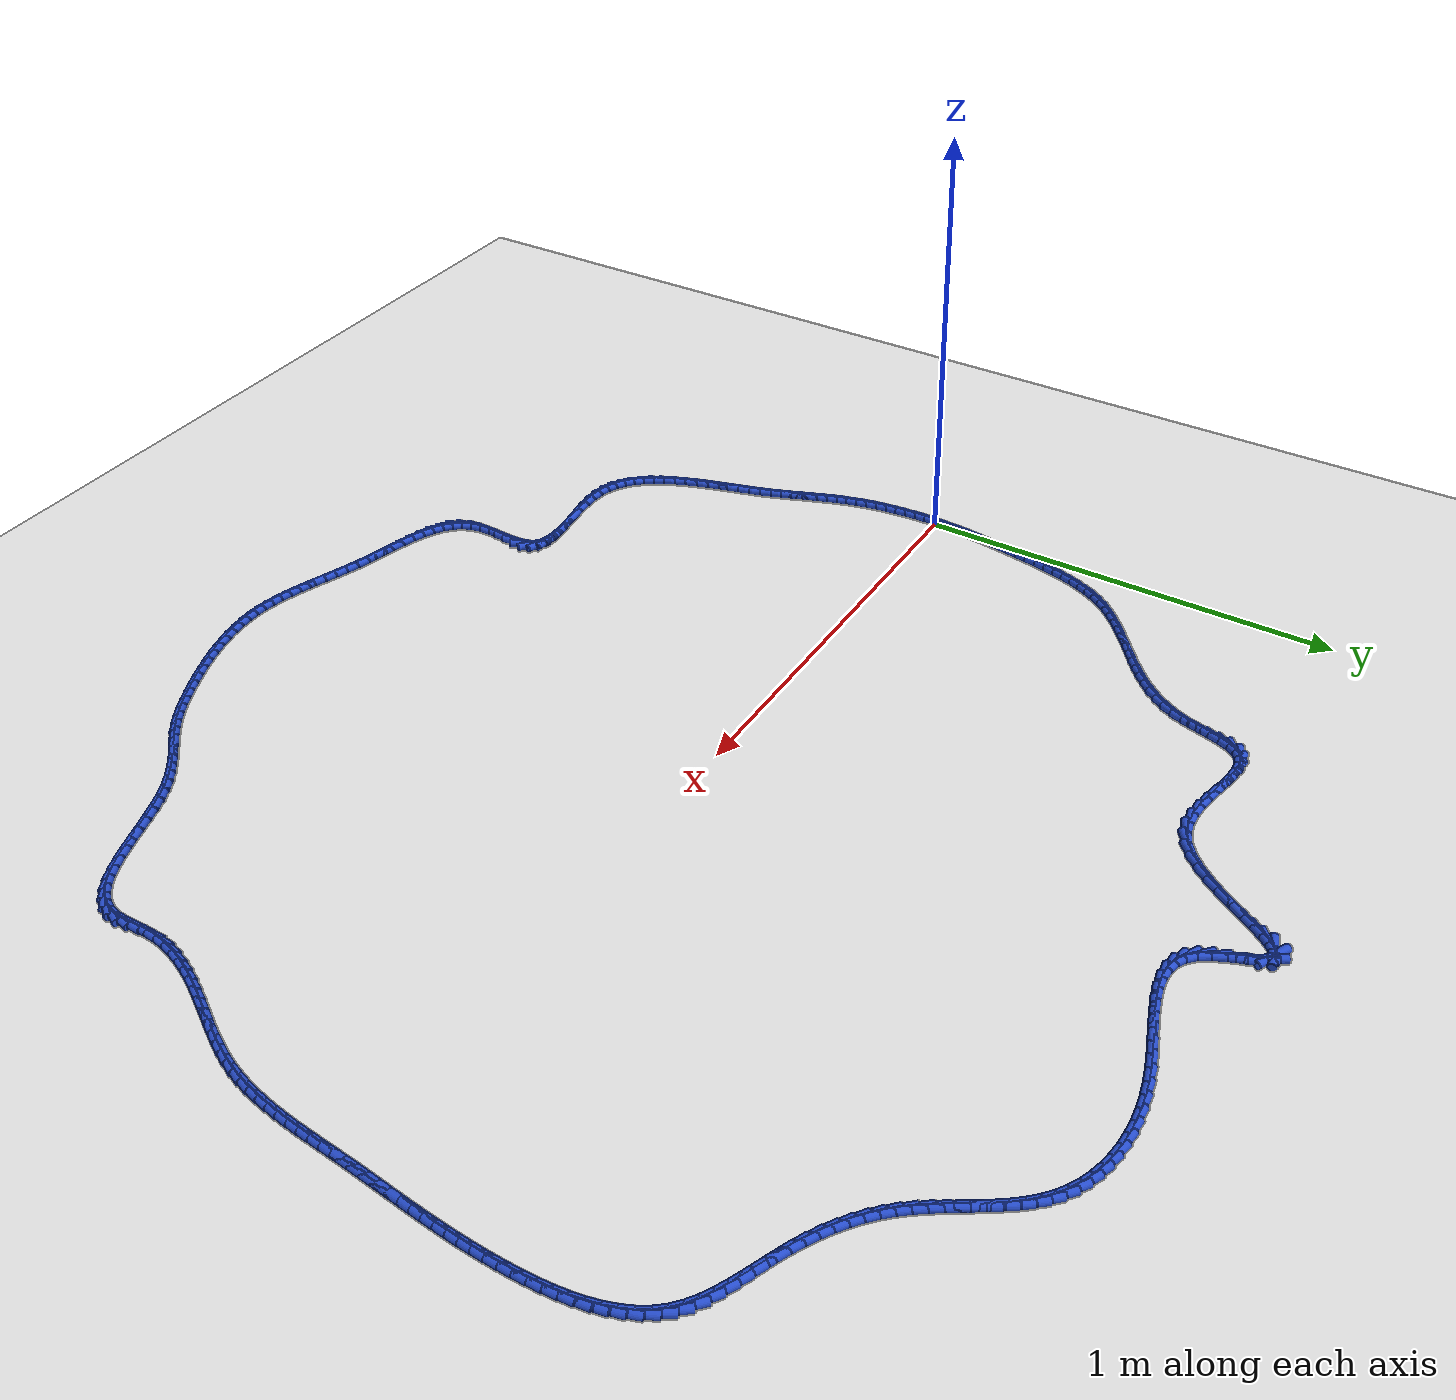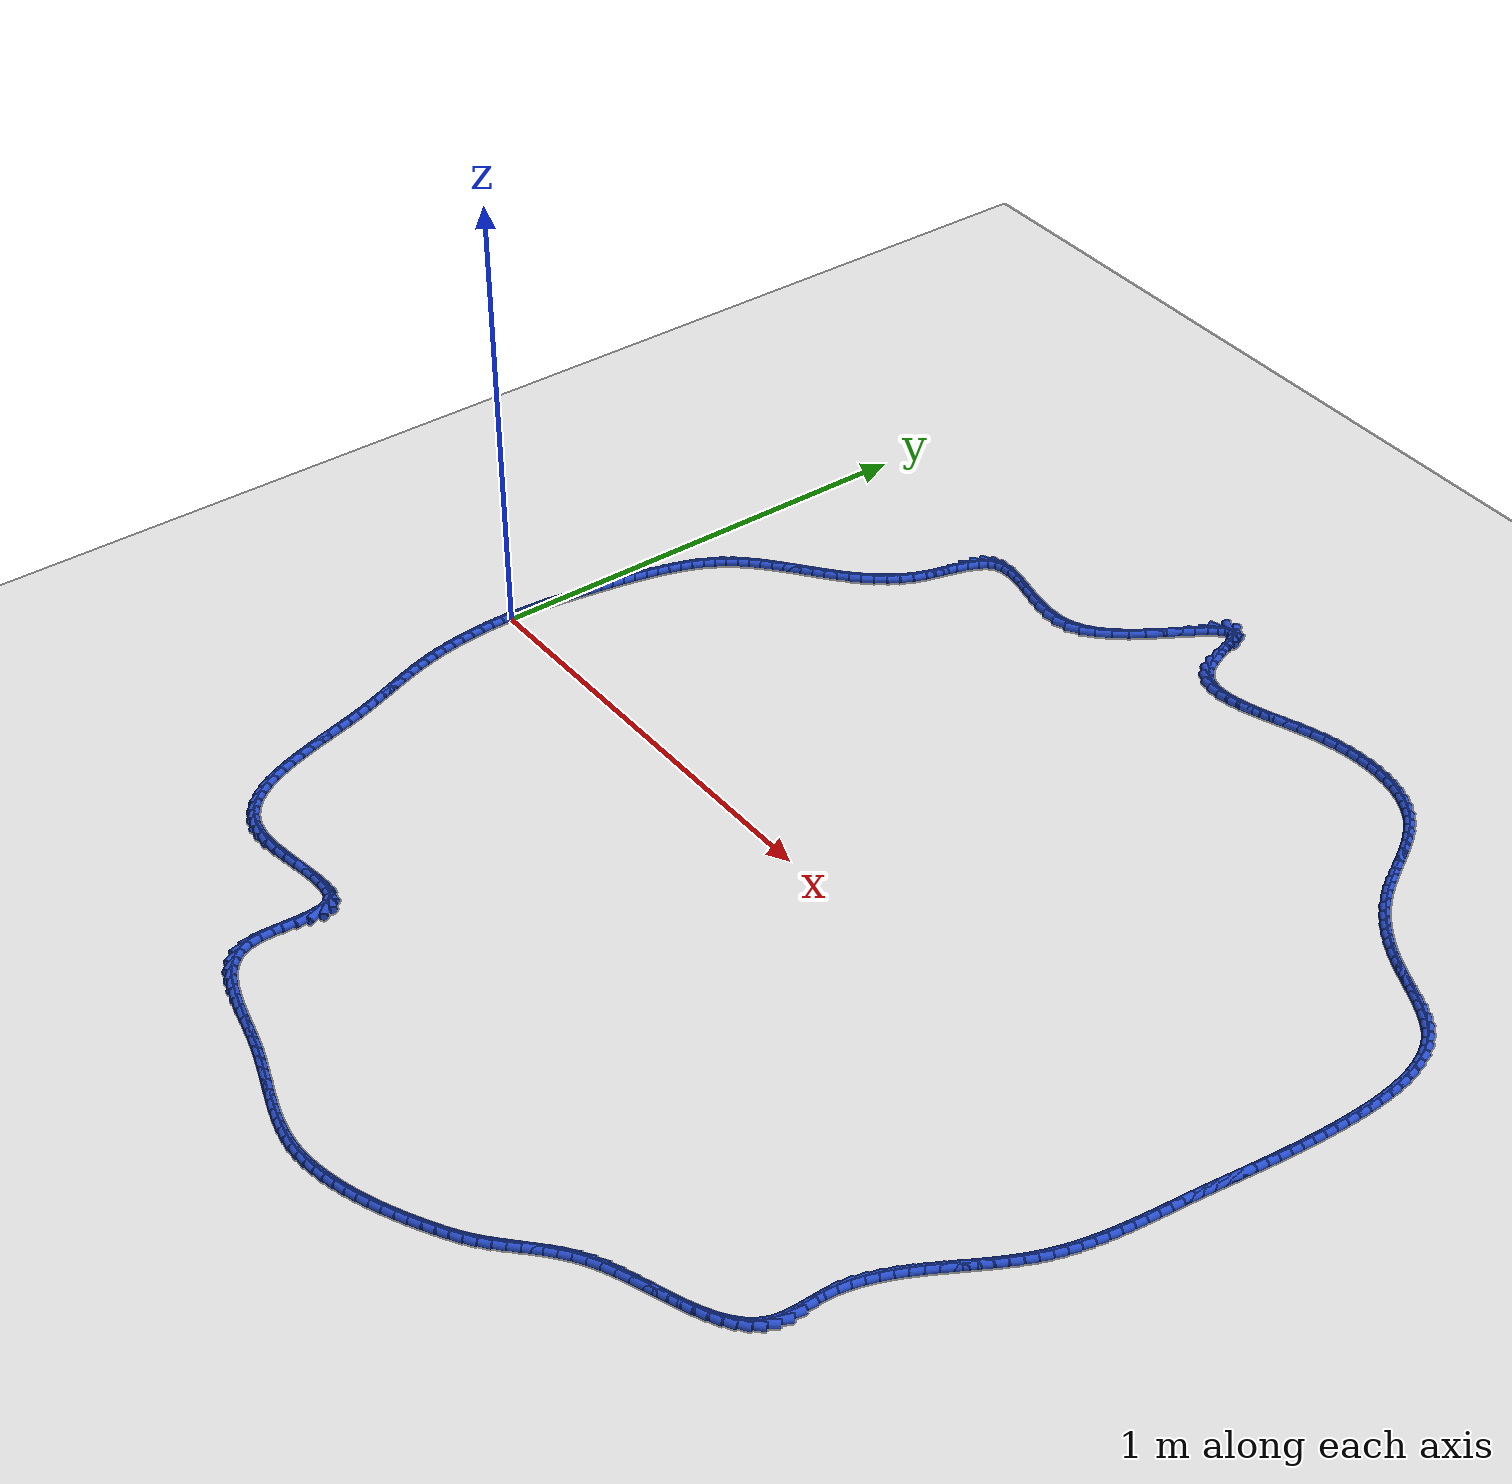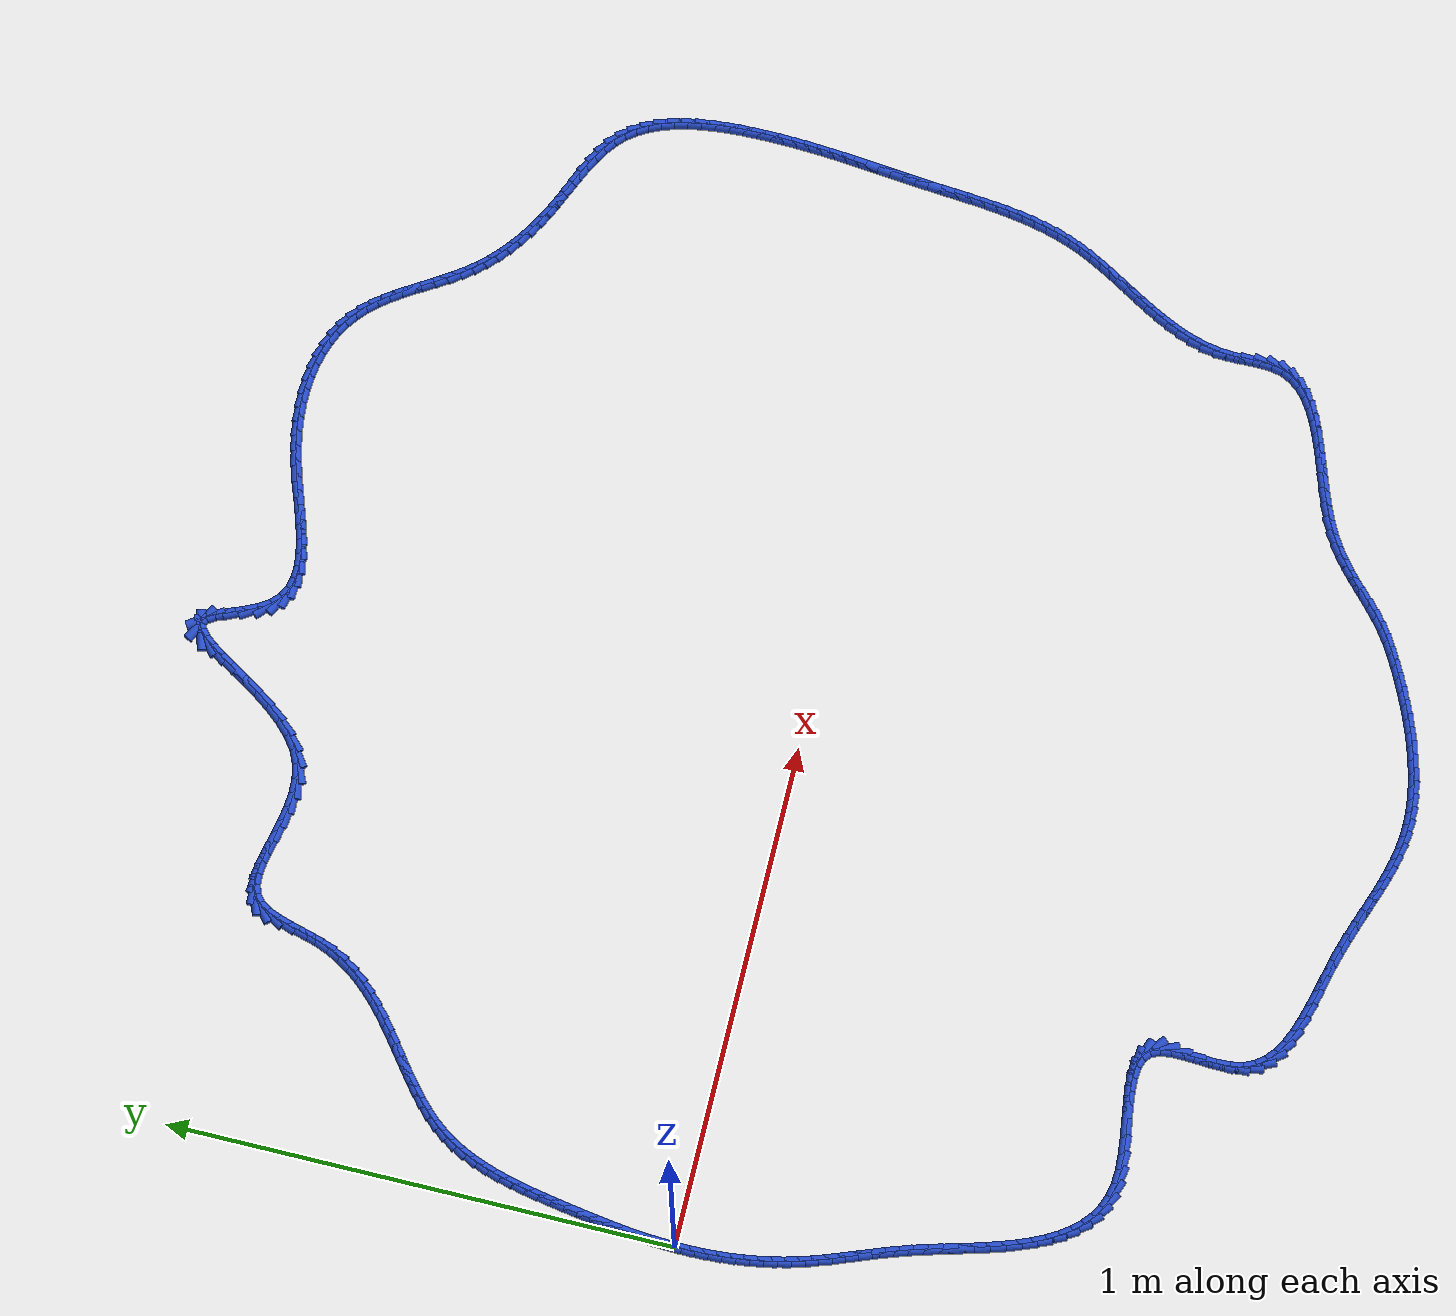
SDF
<sdf version="1.6">
 <world name="default">
  <light name="sun" type="directional">
   <pose>0 0 10 0 -0 0</pose>
   <diffuse>0.8 0.8 0.8 1</diffuse>
   <specular>0.2 0.2 0.2 1</specular>
   <attenuation>
    <range>1000</range>
    <constant>0.9</constant>
    <linear>0.01</linear>
    <quadratic>0.001</quadratic>
   </attenuation>
   <direction>-0.5 0.1 -0.9</direction>
  </light>
  <model name="ground_plane">
   <static>1</static>
   <link name="link">
    <collision name="collision">
     <geometry><plane><normal>0 0 1</normal><size>100 100</size></plane></geometry>
     <surface><friction><ode><mu>100</mu><mu2>50</mu2></ode></friction></surface>
    </collision>
    <visual name="visual">
     <cast_shadows>0</cast_shadows>
     <geometry><plane><normal>0 0 1</normal><size>100 100</size></plane></geometry>
     <material>
      <script><uri>file://media/materials/scripts/gazebo.material</uri><name>Gazebo/WhiteGlow</name></script>
     </material>
    </visual>
   </link>
  </model>
  <gravity>0 0 -9.8</gravity>
  <magnetic_field>6e-06 2.3e-05 -4.2e-05</magnetic_field>
  <atmosphere type="adiabatic"/>
  <physics name="default_physics" default="0" type="ode">
   <max_step_size>0.001</max_step_size>
   <real_time_factor>1</real_time_factor>
   <real_time_update_rate>1000</real_time_update_rate>
  </physics>
  <scene><ambient>0.4 0.4 0.4 1</ambient><background>0.7 0.7 0.7 1</background><shadows>1</shadows></scene>
  <spherical_coordinates>
   <surface_model>EARTH_WGS84</surface_model>
   <latitude_deg>0</latitude_deg>
   <longitude_deg>0</longitude_deg>
   <elevation>0</elevation>
   <heading_deg>0</heading_deg>
  </spherical_coordinates>
  <model name="line">
   <link name="link_0">
    <pose>3.469446951953614e-18 -1.3877787807814457e-17 0.01 0 1.57 1.5349966315205532</pose>
    <collision name="collision">
     <geometry><cylinder><radius>0.01</radius><length>0.08</length></cylinder></geometry>
    </collision>
    <visual name="visual">
     <material>
      <script><name>Gazebo/Blue</name><uri>file://media/materials/scripts/gazebo.material</uri></script>
     </material>
     <geometry><cylinder><radius>0.01</radius><length>0.08</length></cylinder></geometry>
    </visual>
   </link>
   <link name="link_1">
    <pose>0.0009345551304918238 0.026093960901093137 0.01 0 1.57 1.5084178940922301</pose>
    <collision name="collision">
     <geometry><cylinder><radius>0.01</radius><length>0.08</length></cylinder></geometry>
    </collision>
    <visual name="visual">
     <material>
      <script><name>Gazebo/Blue</name><uri>file://media/materials/scripts/gazebo.material</uri></script>
     </material>
     <geometry><cylinder><radius>0.01</radius><length>0.08</length></cylinder></geometry>
    </visual>
   </link>
   <link name="link_2">
    <pose>0.002554962909086989 0.05203731114249139 0.01 0 1.57 1.484605600126524</pose>
    <collision name="collision">
     <geometry><cylinder><radius>0.01</radius><length>0.08</length></cylinder></geometry>
    </collision>
    <visual name="visual">
     <material>
      <script><name>Gazebo/Blue</name><uri>file://media/materials/scripts/gazebo.material</uri></script>
     </material>
     <geometry><cylinder><radius>0.01</radius><length>0.08</length></cylinder></geometry>
    </visual>
   </link>
   <link name="link_3">
    <pose>0.004788108155978377 0.0778824652375783 0.01 0 1.57 1.4637330595707476</pose>
    <collision name="collision">
     <geometry><cylinder><radius>0.01</radius><length>0.08</length></cylinder></geometry>
    </collision>
    <visual name="visual">
     <material>
      <script><name>Gazebo/Blue</name><uri>file://media/materials/scripts/gazebo.material</uri></script>
     </material>
     <geometry><cylinder><radius>0.01</radius><length>0.08</length></cylinder></geometry>
    </visual>
   </link>
   <link name="link_4">
    <pose>0.007560875691358856 0.10368183769973745 0.01 0 1.57 1.445925364941991</pose>
    <collision name="collision">
     <geometry><cylinder><radius>0.01</radius><length>0.08</length></cylinder></geometry>
    </collision>
    <visual name="visual">
     <material>
      <script><name>Gazebo/Blue</name><uri>file://media/materials/scripts/gazebo.material</uri></script>
     </material>
     <geometry><cylinder><radius>0.01</radius><length>0.08</length></cylinder></geometry>
    </visual>
   </link>
   <link name="link_5">
    <pose>0.010800150335421317 0.1294878430423524 0.01 0 1.57 1.4312620993877605</pose>
    <collision name="collision">
     <geometry><cylinder><radius>0.01</radius><length>0.08</length></cylinder></geometry>
    </collision>
    <visual name="visual">
     <material>
      <script><name>Gazebo/Blue</name><uri>file://media/materials/scripts/gazebo.material</uri></script>
     </material>
     <geometry><cylinder><radius>0.01</radius><length>0.08</length></cylinder></geometry>
    </visual>
   </link>
   <link name="link_6">
    <pose>0.014432816908358619 0.15535289577880662 0.01 0 1.57 1.419781155389304</pose>
    <collision name="collision">
     <geometry><cylinder><radius>0.01</radius><length>0.08</length></cylinder></geometry>
    </collision>
    <visual name="visual">
     <material>
      <script><name>Gazebo/Blue</name><uri>file://media/materials/scripts/gazebo.material</uri></script>
     </material>
     <geometry><cylinder><radius>0.01</radius><length>0.08</length></cylinder></geometry>
    </visual>
   </link>
   <link name="link_7">
    <pose>0.018385760230363646 0.18132941042248377 0.01 0 1.57 1.4114830737807074</pose>
    <collision name="collision">
     <geometry><cylinder><radius>0.01</radius><length>0.08</length></cylinder></geometry>
    </collision>
    <visual name="visual">
     <material>
      <script><name>Gazebo/Blue</name><uri>file://media/materials/scripts/gazebo.material</uri></script>
     </material>
     <geometry><cylinder><radius>0.01</radius><length>0.08</length></cylinder></geometry>
    </visual>
   </link>
   <link name="link_8">
    <pose>0.02258586512162927 0.20746980148676736 0.01 0 1.57 1.406204926121847</pose>
    <collision name="collision">
     <geometry><cylinder><radius>0.01</radius><length>0.08</length></cylinder></geometry>
    </collision>
    <visual name="visual">
     <material>
      <script><name>Gazebo/Blue</name><uri>file://media/materials/scripts/gazebo.material</uri></script>
     </material>
     <geometry><cylinder><radius>0.01</radius><length>0.08</length></cylinder></geometry>
    </visual>
   </link>
   <link name="link_9">
    <pose>0.02696309861841557 0.23382376049771153 0.01 0 1.57 1.3995858988335756</pose>
    <collision name="collision">
     <geometry><cylinder><radius>0.01</radius><length>0.08</length></cylinder></geometry>
    </collision>
    <visual name="visual">
     <material>
      <script><name>Gazebo/Blue</name><uri>file://media/materials/scripts/gazebo.material</uri></script>
     </material>
     <geometry><cylinder><radius>0.01</radius><length>0.08</length></cylinder></geometry>
    </visual>
   </link>
   <link name="link_10">
    <pose>0.031549680913267784 0.260350643312851 0.01 0 1.57 1.3864131929045387</pose>
    <collision name="collision">
     <geometry><cylinder><radius>0.01</radius><length>0.08</length></cylinder></geometry>
    </collision>
    <visual name="visual">
     <material>
      <script><name>Gazebo/Blue</name><uri>file://media/materials/scripts/gazebo.material</uri></script>
     </material>
     <geometry><cylinder><radius>0.01</radius><length>0.08</length></cylinder></geometry>
    </visual>
   </link>
   <link name="link_11">
    <pose>0.036501308648437494 0.28690072037821956 0.01 0 1.57 1.366264666740674</pose>
    <collision name="collision">
     <geometry><cylinder><radius>0.01</radius><length>0.08</length></cylinder></geometry>
    </collision>
    <visual name="visual">
     <material>
      <script><name>Gazebo/Blue</name><uri>file://media/materials/scripts/gazebo.material</uri></script>
     </material>
     <geometry><cylinder><radius>0.01</radius><length>0.08</length></cylinder></geometry>
    </visual>
   </link>
   <link name="link_12">
    <pose>0.041981052725971885 0.31331774734155327 0.01 0 1.57 1.3388633902541338</pose>
    <collision name="collision">
     <geometry><cylinder><radius>0.01</radius><length>0.08</length></cylinder></geometry>
    </collision>
    <visual name="visual">
     <material>
      <script><name>Gazebo/Blue</name><uri>file://media/materials/scripts/gazebo.material</uri></script>
     </material>
     <geometry><cylinder><radius>0.01</radius><length>0.08</length></cylinder></geometry>
    </visual>
   </link>
   <link name="link_13">
    <pose>0.048151984047918164 0.33944547985058865 0.01 0 1.57 1.3037849943275877</pose>
    <collision name="collision">
     <geometry><cylinder><radius>0.01</radius><length>0.08</length></cylinder></geometry>
    </collision>
    <visual name="visual">
     <material>
      <script><name>Gazebo/Blue</name><uri>file://media/materials/scripts/gazebo.material</uri></script>
     </material>
     <geometry><cylinder><radius>0.01</radius><length>0.08</length></cylinder></geometry>
    </visual>
   </link>
   <link name="link_14">
    <pose>0.055177173516323515 0.36512767355306164 0.01 0 1.57 1.2604863405628066</pose>
    <collision name="collision">
     <geometry><cylinder><radius>0.01</radius><length>0.08</length></cylinder></geometry>
    </collision>
    <visual name="visual">
     <material>
      <script><name>Gazebo/Blue</name><uri>file://media/materials/scripts/gazebo.material</uri></script>
     </material>
     <geometry><cylinder><radius>0.01</radius><length>0.08</length></cylinder></geometry>
    </visual>
   </link>
   <link name="link_15">
    <pose>0.06321969203323519 0.3902080840967089 0.01 0 1.57 1.2083532021715735</pose>
    <collision name="collision">
     <geometry><cylinder><radius>0.01</radius><length>0.08</length></cylinder></geometry>
    </collision>
    <visual name="visual">
     <material>
      <script><name>Gazebo/Blue</name><uri>file://media/materials/scripts/gazebo.material</uri></script>
     </material>
     <geometry><cylinder><radius>0.01</radius><length>0.08</length></cylinder></geometry>
    </visual>
   </link>
   <link name="link_16">
    <pose>0.07244261050070035 0.4145304671292663 0.01 0 1.57 1.1467799074961422</pose>
    <collision name="collision">
     <geometry><cylinder><radius>0.01</radius><length>0.08</length></cylinder></geometry>
    </collision>
    <visual name="visual">
     <material>
      <script><name>Gazebo/Blue</name><uri>file://media/materials/scripts/gazebo.material</uri></script>
     </material>
     <geometry><cylinder><radius>0.01</radius><length>0.08</length></cylinder></geometry>
    </visual>
   </link>
   <link name="link_17">
    <pose>0.08300899982076619 0.4379385782984703 0.01 0 1.57 1.075294701837149</pose>
    <collision name="collision">
     <geometry><cylinder><radius>0.01</radius><length>0.08</length></cylinder></geometry>
    </collision>
    <visual name="visual">
     <material>
      <script><name>Gazebo/Blue</name><uri>file://media/materials/scripts/gazebo.material</uri></script>
     </material>
     <geometry><cylinder><radius>0.01</radius><length>0.08</length></cylinder></geometry>
    </visual>
   </link>
   <link name="link_18">
    <pose>0.09508193089547992 0.4602761732520572 0.01 0 1.57 0.9937516156851293</pose>
    <collision name="collision">
     <geometry><cylinder><radius>0.01</radius><length>0.08</length></cylinder></geometry>
    </collision>
    <visual name="visual">
     <material>
      <script><name>Gazebo/Blue</name><uri>file://media/materials/scripts/gazebo.material</uri></script>
     </material>
     <geometry><cylinder><radius>0.01</radius><length>0.08</length></cylinder></geometry>
    </visual>
   </link>
   <link name="link_19">
    <pose>0.10882422888578042 0.4813872257412592 0.01 0 1.57 0.9080375376504746</pose>
    <collision name="collision">
     <geometry><cylinder><radius>0.01</radius><length>0.08</length></cylinder></geometry>
    </collision>
    <visual name="visual">
     <material>
      <script><name>Gazebo/Blue</name><uri>file://media/materials/scripts/gazebo.material</uri></script>
     </material>
     <geometry><cylinder><radius>0.01</radius><length>0.08</length></cylinder></geometry>
    </visual>
   </link>
   <link name="link_20">
    <pose>0.12429491190765735 0.5012078417598891 0.01 0 1.57 0.8331925428434346</pose>
    <collision name="collision">
     <geometry><cylinder><radius>0.01</radius><length>0.08</length></cylinder></geometry>
    </collision>
    <visual name="visual">
     <material>
      <script><name>Gazebo/Blue</name><uri>file://media/materials/scripts/gazebo.material</uri></script>
     </material>
     <geometry><cylinder><radius>0.01</radius><length>0.08</length></cylinder></geometry>
    </visual>
   </link>
   <link name="link_21">
    <pose>0.14128857700210487 0.5199088098961528 0.01 0 1.57 0.7720643885398846</pose>
    <collision name="collision">
     <geometry><cylinder><radius>0.01</radius><length>0.08</length></cylinder></geometry>
    </collision>
    <visual name="visual">
     <material>
      <script><name>Gazebo/Blue</name><uri>file://media/materials/scripts/gazebo.material</uri></script>
     </material>
     <geometry><cylinder><radius>0.01</radius><length>0.08</length></cylinder></geometry>
    </visual>
   </link>
   <link name="link_22">
    <pose>0.15955833402631928 0.5376977400087541 0.01 0 1.57 0.7246087713500247</pose>
    <collision name="collision">
     <geometry><cylinder><radius>0.01</radius><length>0.08</length></cylinder></geometry>
    </collision>
    <visual name="visual">
     <material>
      <script><name>Gazebo/Blue</name><uri>file://media/materials/scripts/gazebo.material</uri></script>
     </material>
     <geometry><cylinder><radius>0.01</radius><length>0.08</length></cylinder></geometry>
    </visual>
   </link>
   <link name="link_23">
    <pose>0.17885729283749688 0.5547822419563966 0.01 0 1.57 0.69041117564255</pose>
    <collision name="collision">
     <geometry><cylinder><radius>0.01</radius><length>0.08</length></cylinder></geometry>
    </collision>
    <visual name="visual">
     <material>
      <script><name>Gazebo/Blue</name><uri>file://media/materials/scripts/gazebo.material</uri></script>
     </material>
     <geometry><cylinder><radius>0.01</radius><length>0.08</length></cylinder></geometry>
    </visual>
   </link>
   <link name="link_24">
    <pose>0.198938563292834 0.5713699255977841 0.01 0 1.57 0.66895061508409</pose>
    <collision name="collision">
     <geometry><cylinder><radius>0.01</radius><length>0.08</length></cylinder></geometry>
    </collision>
    <visual name="visual">
     <material>
      <script><name>Gazebo/Blue</name><uri>file://media/materials/scripts/gazebo.material</uri></script>
     </material>
     <geometry><cylinder><radius>0.01</radius><length>0.08</length></cylinder></geometry>
    </visual>
   </link>
   <link name="link_25">
    <pose>0.2195552552495269 0.58766840079162 0.01 0 1.57 0.6597680014727794</pose>
    <collision name="collision">
     <geometry><cylinder><radius>0.01</radius><length>0.08</length></cylinder></geometry>
    </collision>
    <visual name="visual">
     <material>
      <script><name>Gazebo/Blue</name><uri>file://media/materials/scripts/gazebo.material</uri></script>
     </material>
     <geometry><cylinder><radius>0.01</radius><length>0.08</length></cylinder></geometry>
    </visual>
   </link>
   <link name="link_26">
    <pose>0.24046047856477193 0.603885277396608 0.01 0 1.57 0.6625549072321429</pose>
    <collision name="collision">
     <geometry><cylinder><radius>0.01</radius><length>0.08</length></cylinder></geometry>
    </collision>
    <visual name="visual">
     <material>
      <script><name>Gazebo/Blue</name><uri>file://media/materials/scripts/gazebo.material</uri></script>
     </material>
     <geometry><cylinder><radius>0.01</radius><length>0.08</length></cylinder></geometry>
    </visual>
   </link>
   <link name="link_27">
    <pose>0.26140734309576535 0.6202281652714523 0.01 0 1.57 0.677182534440346</pose>
    <collision name="collision">
     <geometry><cylinder><radius>0.01</radius><length>0.08</length></cylinder></geometry>
    </collision>
    <visual name="visual">
     <material>
      <script><name>Gazebo/Blue</name><uri>file://media/materials/scripts/gazebo.material</uri></script>
     </material>
     <geometry><cylinder><radius>0.01</radius><length>0.08</length></cylinder></geometry>
    </visual>
   </link>
   <link name="link_28">
    <pose>0.28214895869970336 0.6369046742748554 0.01 0 1.57 0.7036833149951631</pose>
    <collision name="collision">
     <geometry><cylinder><radius>0.01</radius><length>0.08</length></cylinder></geometry>
    </collision>
    <visual name="visual">
     <material>
      <script><name>Gazebo/Blue</name><uri>file://media/materials/scripts/gazebo.material</uri></script>
     </material>
     <geometry><cylinder><radius>0.01</radius><length>0.08</length></cylinder></geometry>
    </visual>
   </link>
   <link name="link_29">
    <pose>0.3024384352337828 0.6541224142655224 0.01 0 1.57 0.7421877238234136</pose>
    <collision name="collision">
     <geometry><cylinder><radius>0.01</radius><length>0.08</length></cylinder></geometry>
    </collision>
    <visual name="visual">
     <material>
      <script><name>Gazebo/Blue</name><uri>file://media/materials/scripts/gazebo.material</uri></script>
     </material>
     <geometry><cylinder><radius>0.01</radius><length>0.08</length></cylinder></geometry>
    </visual>
   </link>
   <link name="link_30">
    <pose>0.3220288825551993 0.6720889951021563 0.01 0 1.57 0.7928114337062153</pose>
    <collision name="collision">
     <geometry><cylinder><radius>0.01</radius><length>0.08</length></cylinder></geometry>
    </collision>
    <visual name="visual">
     <material>
      <script><name>Gazebo/Blue</name><uri>file://media/materials/scripts/gazebo.material</uri></script>
     </material>
     <geometry><cylinder><radius>0.01</radius><length>0.08</length></cylinder></geometry>
    </visual>
   </link>
   <link name="link_31">
    <pose>0.3406734105211495 0.6910120266434608 0.01 0 1.57 0.8554871403688812</pose>
    <collision name="collision">
     <geometry><cylinder><radius>0.01</radius><length>0.08</length></cylinder></geometry>
    </collision>
    <visual name="visual">
     <material>
      <script><name>Gazebo/Blue</name><uri>file://media/materials/scripts/gazebo.material</uri></script>
     </material>
     <geometry><cylinder><radius>0.01</radius><length>0.08</length></cylinder></geometry>
    </visual>
   </link>
   <link name="link_32">
    <pose>0.35812512898882964 0.7110991187481395 0.01 0 1.57 0.9297469166885302</pose>
    <collision name="collision">
     <geometry><cylinder><radius>0.01</radius><length>0.08</length></cylinder></geometry>
    </collision>
    <visual name="visual">
     <material>
      <script><name>Gazebo/Blue</name><uri>file://media/materials/scripts/gazebo.material</uri></script>
     </material>
     <geometry><cylinder><radius>0.01</radius><length>0.08</length></cylinder></geometry>
    </visual>
   </link>
   <link name="link_33">
    <pose>0.3741371478154362 0.7325578812748964 0.01 0 1.57 1.0144897370281505</pose>
    <collision name="collision">
     <geometry><cylinder><radius>0.01</radius><length>0.08</length></cylinder></geometry>
    </collision>
    <visual name="visual">
     <material>
      <script><name>Gazebo/Blue</name><uri>file://media/materials/scripts/gazebo.material</uri></script>
     </material>
     <geometry><cylinder><radius>0.01</radius><length>0.08</length></cylinder></geometry>
    </visual>
   </link>
   <link name="link_34">
    <pose>0.3884625768581652 0.7555959240824348 0.01 0 1.57 1.1078101218638767</pose>
    <collision name="collision">
     <geometry><cylinder><radius>0.01</radius><length>0.08</length></cylinder></geometry>
    </collision>
    <visual name="visual">
     <material>
      <script><name>Gazebo/Blue</name><uri>file://media/materials/scripts/gazebo.material</uri></script>
     </material>
     <geometry><cylinder><radius>0.01</radius><length>0.08</length></cylinder></geometry>
    </visual>
   </link>
   <link name="link_35">
    <pose>0.4008545259742131 0.7804208570294588 0.01 0 1.57 1.2062532085887105</pose>
    <collision name="collision">
     <geometry><cylinder><radius>0.01</radius><length>0.08</length></cylinder></geometry>
    </collision>
    <visual name="visual">
     <material>
      <script><name>Gazebo/Blue</name><uri>file://media/materials/scripts/gazebo.material</uri></script>
     </material>
     <geometry><cylinder><radius>0.01</radius><length>0.08</length></cylinder></geometry>
    </visual>
   </link>
   <link name="link_36">
    <pose>0.411081138819443 0.8072202583912982 0.01 0 1.57 1.2818337409455303</pose>
    <collision name="collision">
     <geometry><cylinder><radius>0.01</radius><length>0.08</length></cylinder></geometry>
    </collision>
    <visual name="visual">
     <material>
      <script><name>Gazebo/Blue</name><uri>file://media/materials/scripts/gazebo.material</uri></script>
     </material>
     <geometry><cylinder><radius>0.01</radius><length>0.08</length></cylinder></geometry>
    </visual>
   </link>
   <link name="link_37">
    <pose>0.41946949430584796 0.8354369606586894 0.01 0 1.57 1.307279557385827</pose>
    <collision name="collision">
     <geometry><cylinder><radius>0.01</radius><length>0.08</length></cylinder></geometry>
    </collision>
    <visual name="visual">
     <material>
      <script><name>Gazebo/Blue</name><uri>file://media/materials/scripts/gazebo.material</uri></script>
     </material>
     <geometry><cylinder><radius>0.01</radius><length>0.08</length></cylinder></geometry>
    </visual>
   </link>
   <link name="link_38">
    <pose>0.427058328923056 0.8635655577290681 0.01 0 1.57 1.2816940469838736</pose>
    <collision name="collision">
     <geometry><cylinder><radius>0.01</radius><length>0.08</length></cylinder></geometry>
    </collision>
    <visual name="visual">
     <material>
      <script><name>Gazebo/Blue</name><uri>file://media/materials/scripts/gazebo.material</uri></script>
     </material>
     <geometry><cylinder><radius>0.01</radius><length>0.08</length></cylinder></geometry>
    </visual>
   </link>
   <link name="link_39">
    <pose>0.4349325172396189 0.8900391674354967 0.01 0 1.57 1.1923782774701637</pose>
    <collision name="collision">
     <geometry><cylinder><radius>0.01</radius><length>0.08</length></cylinder></geometry>
    </collision>
    <visual name="visual">
     <material>
      <script><name>Gazebo/Blue</name><uri>file://media/materials/scripts/gazebo.material</uri></script>
     </material>
     <geometry><cylinder><radius>0.01</radius><length>0.08</length></cylinder></geometry>
    </visual>
   </link>
   <link name="link_40">
    <pose>0.4441769338240876 0.9132909076110352 0.01 0 1.57 1.0059836887501532</pose>
    <collision name="collision">
     <geometry><cylinder><radius>0.01</radius><length>0.08</length></cylinder></geometry>
    </collision>
    <visual name="visual">
     <material>
      <script><name>Gazebo/Blue</name><uri>file://media/materials/scripts/gazebo.material</uri></script>
     </material>
     <geometry><cylinder><radius>0.01</radius><length>0.08</length></cylinder></geometry>
    </visual>
   </link>
   <link name="link_41">
    <pose>0.4558764532450137 0.9317538960887456 0.01 0 1.57 0.6781198555130753</pose>
    <collision name="collision">
     <geometry><cylinder><radius>0.01</radius><length>0.08</length></cylinder></geometry>
    </collision>
    <visual name="visual">
     <material>
      <script><name>Gazebo/Blue</name><uri>file://media/materials/scripts/gazebo.material</uri></script>
     </material>
     <geometry><cylinder><radius>0.01</radius><length>0.08</length></cylinder></geometry>
    </visual>
   </link>
   <link name="link_42">
    <pose>0.47105002976970356 0.9439770686609245 0.01 0 1.57 0.3132557845495781</pose>
    <collision name="collision">
     <geometry><cylinder><radius>0.01</radius><length>0.08</length></cylinder></geometry>
    </collision>
    <visual name="visual">
     <material>
      <script><name>Gazebo/Blue</name><uri>file://media/materials/scripts/gazebo.material</uri></script>
     </material>
     <geometry><cylinder><radius>0.01</radius><length>0.08</length></cylinder></geometry>
    </visual>
   </link>
   <link name="link_43">
    <pose>0.4898332662802066 0.9500613557678835 0.01 0 1.57 0.05268638335929797</pose>
    <collision name="collision">
     <geometry><cylinder><radius>0.01</radius><length>0.08</length></cylinder></geometry>
    </collision>
    <visual name="visual">
     <material>
      <script><name>Gazebo/Blue</name><uri>file://media/materials/scripts/gazebo.material</uri></script>
     </material>
     <geometry><cylinder><radius>0.01</radius><length>0.08</length></cylinder></geometry>
    </visual>
   </link>
   <link name="link_44">
    <pose>0.5117308717341985 0.9512161300966295 0.01 0 1.57 -0.10334899234721864</pose>
    <collision name="collision">
     <geometry><cylinder><radius>0.01</radius><length>0.08</length></cylinder></geometry>
    </collision>
    <visual name="visual">
     <material>
      <script><name>Gazebo/Blue</name><uri>file://media/materials/scripts/gazebo.material</uri></script>
     </material>
     <geometry><cylinder><radius>0.01</radius><length>0.08</length></cylinder></geometry>
    </visual>
   </link>
   <link name="link_45">
    <pose>0.5362339262739055 0.9486747093338458 0.01 0 1.57 -0.18596078595667456</pose>
    <collision name="collision">
     <geometry><cylinder><radius>0.01</radius><length>0.08</length></cylinder></geometry>
    </collision>
    <visual name="visual">
     <material>
      <script><name>Gazebo/Blue</name><uri>file://media/materials/scripts/gazebo.material</uri></script>
     </material>
     <geometry><cylinder><radius>0.01</radius><length>0.08</length></cylinder></geometry>
    </visual>
   </link>
   <link name="link_46">
    <pose>0.5628335100415547 0.9436704111662171 0.01 0 1.57 -0.21765574758407233</pose>
    <collision name="collision">
     <geometry><cylinder><radius>0.01</radius><length>0.08</length></cylinder></geometry>
    </collision>
    <visual name="visual">
     <material>
      <script><name>Gazebo/Blue</name><uri>file://media/materials/scripts/gazebo.material</uri></script>
     </material>
     <geometry><cylinder><radius>0.01</radius><length>0.08</length></cylinder></geometry>
    </visual>
   </link>
   <link name="link_47">
    <pose>0.5910207031793724 0.9374365532804272 0.01 0 1.57 -0.2097482544717887</pose>
    <collision name="collision">
     <geometry><cylinder><radius>0.01</radius><length>0.08</length></cylinder></geometry>
    </collision>
    <visual name="visual">
     <material>
      <script><name>Gazebo/Blue</name><uri>file://media/materials/scripts/gazebo.material</uri></script>
     </material>
     <geometry><cylinder><radius>0.01</radius><length>0.08</length></cylinder></geometry>
    </visual>
   </link>
   <link name="link_48">
    <pose>0.6202865858295856 0.9312064533631601 0.01 0 1.57 -0.16581437649481212</pose>
    <collision name="collision">
     <geometry><cylinder><radius>0.01</radius><length>0.08</length></cylinder></geometry>
    </collision>
    <visual name="visual">
     <material>
      <script><name>Gazebo/Blue</name><uri>file://media/materials/scripts/gazebo.material</uri></script>
     </material>
     <geometry><cylinder><radius>0.01</radius><length>0.08</length></cylinder></geometry>
    </visual>
   </link>
   <link name="link_49">
    <pose>0.6501222381344205 0.9262134291010994 0.01 0 1.57 -0.08417939653752603</pose>
    <collision name="collision">
     <geometry><cylinder><radius>0.01</radius><length>0.08</length></cylinder></geometry>
    </collision>
    <visual name="visual">
     <material>
      <script><name>Gazebo/Blue</name><uri>file://media/materials/scripts/gazebo.material</uri></script>
     </material>
     <geometry><cylinder><radius>0.01</radius><length>0.08</length></cylinder></geometry>
    </visual>
   </link>
   <link name="link_50">
    <pose>0.6800187402361043 0.9236907981809298 0.01 0 1.57 0.04008523924446155</pose>
    <collision name="collision">
     <geometry><cylinder><radius>0.01</radius><length>0.08</length></cylinder></geometry>
    </collision>
    <visual name="visual">
     <material>
      <script><name>Gazebo/Blue</name><uri>file://media/materials/scripts/gazebo.material</uri></script>
     </material>
     <geometry><cylinder><radius>0.01</radius><length>0.08</length></cylinder></geometry>
    </visual>
   </link>
   <link name="link_51">
    <pose>0.7094671722768634 0.9248718782893348 0.01 0 1.57 0.21152282106985118</pose>
    <collision name="collision">
     <geometry><cylinder><radius>0.01</radius><length>0.08</length></cylinder></geometry>
    </collision>
    <visual name="visual">
     <material>
      <script><name>Gazebo/Blue</name><uri>file://media/materials/scripts/gazebo.material</uri></script>
     </material>
     <geometry><cylinder><radius>0.01</radius><length>0.08</length></cylinder></geometry>
    </visual>
   </link>
   <link name="link_52">
    <pose>0.7379586143989245 0.9309899871129986 0.01 0 1.57 0.42581569554812954</pose>
    <collision name="collision">
     <geometry><cylinder><radius>0.01</radius><length>0.08</length></cylinder></geometry>
    </collision>
    <visual name="visual">
     <material>
      <script><name>Gazebo/Blue</name><uri>file://media/materials/scripts/gazebo.material</uri></script>
     </material>
     <geometry><cylinder><radius>0.01</radius><length>0.08</length></cylinder></geometry>
    </visual>
   </link>
   <link name="link_53">
    <pose>0.764990262229206 0.9432506313668181 0.01 0 1.57 0.6314356508092364</pose>
    <collision name="collision">
     <geometry><cylinder><radius>0.01</radius><length>0.08</length></cylinder></geometry>
    </collision>
    <visual name="visual">
     <material>
      <script><name>Gazebo/Blue</name><uri>file://media/materials/scripts/gazebo.material</uri></script>
     </material>
     <geometry><cylinder><radius>0.01</radius><length>0.08</length></cylinder></geometry>
    </visual>
   </link>
   <link name="link_54">
    <pose>0.7903008922017769 0.9617606972391546 0.01 0 1.57 0.7808220849235016</pose>
    <collision name="collision">
     <geometry><cylinder><radius>0.01</radius><length>0.08</length></cylinder></geometry>
    </collision>
    <visual name="visual">
     <material>
      <script><name>Gazebo/Blue</name><uri>file://media/materials/scripts/gazebo.material</uri></script>
     </material>
     <geometry><cylinder><radius>0.01</radius><length>0.08</length></cylinder></geometry>
    </visual>
   </link>
   <link name="link_55">
    <pose>0.8139453433014411 0.9851897348567823 0.01 0 1.57 0.8844302414726082</pose>
    <collision name="collision">
     <geometry><cylinder><radius>0.01</radius><length>0.08</length></cylinder></geometry>
    </collision>
    <visual name="visual">
     <material>
      <script><name>Gazebo/Blue</name><uri>file://media/materials/scripts/gazebo.material</uri></script>
     </material>
     <geometry><cylinder><radius>0.01</radius><length>0.08</length></cylinder></geometry>
    </visual>
   </link>
   <link name="link_56">
    <pose>0.8359998044002391 1.0121102029233804 0.01 0 1.57 0.9542679930613137</pose>
    <collision name="collision">
     <geometry><cylinder><radius>0.01</radius><length>0.08</length></cylinder></geometry>
    </collision>
    <visual name="visual">
     <material>
      <script><name>Gazebo/Blue</name><uri>file://media/materials/scripts/gazebo.material</uri></script>
     </material>
     <geometry><cylinder><radius>0.01</radius><length>0.08</length></cylinder></geometry>
    </visual>
   </link>
   <link name="link_57">
    <pose>0.856540464370212 1.0410945601426285 0.01 0 1.57 0.9979990848718903</pose>
    <collision name="collision">
     <geometry><cylinder><radius>0.01</radius><length>0.08</length></cylinder></geometry>
    </collision>
    <visual name="visual">
     <material>
      <script><name>Gazebo/Blue</name><uri>file://media/materials/scripts/gazebo.material</uri></script>
     </material>
     <geometry><cylinder><radius>0.01</radius><length>0.08</length></cylinder></geometry>
    </visual>
   </link>
   <link name="link_58">
    <pose>0.8756435120834011 1.070715265218205 0.01 0 1.57 1.0191316229129577</pose>
    <collision name="collision">
     <geometry><cylinder><radius>0.01</radius><length>0.08</length></cylinder></geometry>
    </collision>
    <visual name="visual">
     <material>
      <script><name>Gazebo/Blue</name><uri>file://media/materials/scripts/gazebo.material</uri></script>
     </material>
     <geometry><cylinder><radius>0.01</radius><length>0.08</length></cylinder></geometry>
    </visual>
   </link>
   <link name="link_59">
    <pose>0.8933851364118472 1.0995447768537903 0.01 0 1.57 1.016949405440842</pose>
    <collision name="collision">
     <geometry><cylinder><radius>0.01</radius><length>0.08</length></cylinder></geometry>
    </collision>
    <visual name="visual">
     <material>
      <script><name>Gazebo/Blue</name><uri>file://media/materials/scripts/gazebo.material</uri></script>
     </material>
     <geometry><cylinder><radius>0.01</radius><length>0.08</length></cylinder></geometry>
    </visual>
   </link>
   <link name="link_60">
    <pose>0.9098415262275917 1.1261555537530628 0.01 0 1.57 0.9846749224691254</pose>
    <collision name="collision">
     <geometry><cylinder><radius>0.01</radius><length>0.08</length></cylinder></geometry>
    </collision>
    <visual name="visual">
     <material>
      <script><name>Gazebo/Blue</name><uri>file://media/materials/scripts/gazebo.material</uri></script>
     </material>
     <geometry><cylinder><radius>0.01</radius><length>0.08</length></cylinder></geometry>
    </visual>
   </link>
   <link name="link_61">
    <pose>0.9250888704026756 1.149120054619702 0.01 0 1.57 0.9028422575319455</pose>
    <collision name="collision">
     <geometry><cylinder><radius>0.01</radius><length>0.08</length></cylinder></geometry>
    </collision>
    <visual name="visual">
     <material>
      <script><name>Gazebo/Blue</name><uri>file://media/materials/scripts/gazebo.material</uri></script>
     </material>
     <geometry><cylinder><radius>0.01</radius><length>0.08</length></cylinder></geometry>
    </visual>
   </link>
   <link name="link_62">
    <pose>0.9392033578091397 1.1670107381573873 0.01 0 1.57 0.7172547759534537</pose>
    <collision name="collision">
     <geometry><cylinder><radius>0.01</radius><length>0.08</length></cylinder></geometry>
    </collision>
    <visual name="visual">
     <material>
      <script><name>Gazebo/Blue</name><uri>file://media/materials/scripts/gazebo.material</uri></script>
     </material>
     <geometry><cylinder><radius>0.01</radius><length>0.08</length></cylinder></geometry>
    </visual>
   </link>
   <link name="link_63">
    <pose>0.952261177319025 1.1784000630697977 0.01 0 1.57 0.2790463491939582</pose>
    <collision name="collision">
     <geometry><cylinder><radius>0.01</radius><length>0.08</length></cylinder></geometry>
    </collision>
    <visual name="visual">
     <material>
      <script><name>Gazebo/Blue</name><uri>file://media/materials/scripts/gazebo.material</uri></script>
     </material>
     <geometry><cylinder><radius>0.01</radius><length>0.08</length></cylinder></geometry>
    </visual>
   </link>
   <link name="link_64">
    <pose>0.9643385178043727 1.1818604880606123 0.01 0 1.57 -0.4855610881498735</pose>
    <collision name="collision">
     <geometry><cylinder><radius>0.01</radius><length>0.08</length></cylinder></geometry>
    </collision>
    <visual name="visual">
     <material>
      <script><name>Gazebo/Blue</name><uri>file://media/materials/scripts/gazebo.material</uri></script>
     </material>
     <geometry><cylinder><radius>0.01</radius><length>0.08</length></cylinder></geometry>
    </visual>
   </link>
   <link name="link_65">
    <pose>0.9755115681372244 1.1759644718335114 0.01 0 1.57 -0.9906905959709252</pose>
    <collision name="collision">
     <geometry><cylinder><radius>0.01</radius><length>0.08</length></cylinder></geometry>
    </collision>
    <visual name="visual">
     <material>
      <script><name>Gazebo/Blue</name><uri>file://media/materials/scripts/gazebo.material</uri></script>
     </material>
     <geometry><cylinder><radius>0.01</radius><length>0.08</length></cylinder></geometry>
    </visual>
   </link>
   <link name="link_66">
    <pose>0.9859562282229589 1.1600262021842145 0.01 0 1.57 -1.1520627366846383</pose>
    <collision name="collision">
     <geometry><cylinder><radius>0.01</radius><length>0.08</length></cylinder></geometry>
    </collision>
    <visual name="visual">
     <material>
      <script><name>Gazebo/Blue</name><uri>file://media/materials/scripts/gazebo.material</uri></script>
     </material>
     <geometry><cylinder><radius>0.01</radius><length>0.08</length></cylinder></geometry>
    </visual>
   </link>
   <link name="link_67">
    <pose>0.9963067497824023 1.1367694482207973 0.01 0 1.57 -1.1815532201795544</pose>
    <collision name="collision">
     <geometry><cylinder><radius>0.01</radius><length>0.08</length></cylinder></geometry>
    </collision>
    <visual name="visual">
     <material>
      <script><name>Gazebo/Blue</name><uri>file://media/materials/scripts/gazebo.material</uri></script>
     </material>
     <geometry><cylinder><radius>0.01</radius><length>0.08</length></cylinder></geometry>
    </visual>
   </link>
   <link name="link_68">
    <pose>1.0073290042139862 1.1098970697366533 0.01 0 1.57 -1.1353907675519321</pose>
    <collision name="collision">
     <geometry><cylinder><radius>0.01</radius><length>0.08</length></cylinder></geometry>
    </collision>
    <visual name="visual">
     <material>
      <script><name>Gazebo/Blue</name><uri>file://media/materials/scripts/gazebo.material</uri></script>
     </material>
     <geometry><cylinder><radius>0.01</radius><length>0.08</length></cylinder></geometry>
    </visual>
   </link>
   <link name="link_69">
    <pose>1.0197888743236885 1.0831120113834767 0.01 0 1.57 -1.0031923334823036</pose>
    <collision name="collision">
     <geometry><cylinder><radius>0.01</radius><length>0.08</length></cylinder></geometry>
    </collision>
    <visual name="visual">
     <material>
      <script><name>Gazebo/Blue</name><uri>file://media/materials/scripts/gazebo.material</uri></script>
     </material>
     <geometry><cylinder><radius>0.01</radius><length>0.08</length></cylinder></geometry>
    </visual>
   </link>
   <link name="link_70">
    <pose>1.034451697675095 1.0601148714902073 0.01 0 1.57 -0.7633360362596646</pose>
    <collision name="collision">
     <geometry><cylinder><radius>0.01</radius><length>0.08</length></cylinder></geometry>
    </collision>
    <visual name="visual">
     <material>
      <script><name>Gazebo/Blue</name><uri>file://media/materials/scripts/gazebo.material</uri></script>
     </material>
     <geometry><cylinder><radius>0.01</radius><length>0.08</length></cylinder></geometry>
    </visual>
   </link>
   <link name="link_71">
    <pose>1.0518240321882353 1.0434926508809628 0.01 0 1.57 -0.4871833351723494</pose>
    <collision name="collision">
     <geometry><cylinder><radius>0.01</radius><length>0.08</length></cylinder></geometry>
    </collision>
    <visual name="visual">
     <material>
      <script><name>Gazebo/Blue</name><uri>file://media/materials/scripts/gazebo.material</uri></script>
     </material>
     <geometry><cylinder><radius>0.01</radius><length>0.08</length></cylinder></geometry>
    </visual>
   </link>
   <link name="link_72">
    <pose>1.0717406160468312 1.0329413317056149 0.01 0 1.57 -0.23223525083887703</pose>
    <collision name="collision">
     <geometry><cylinder><radius>0.01</radius><length>0.08</length></cylinder></geometry>
    </collision>
    <visual name="visual">
     <material>
      <script><name>Gazebo/Blue</name><uri>file://media/materials/scripts/gazebo.material</uri></script>
     </material>
     <geometry><cylinder><radius>0.01</radius><length>0.08</length></cylinder></geometry>
    </visual>
   </link>
   <link name="link_73">
    <pose>1.093928578310569 1.0276938254861652 0.01 0 1.57 -0.029379121388368363</pose>
    <collision name="collision">
     <geometry><cylinder><radius>0.01</radius><length>0.08</length></cylinder></geometry>
    </collision>
    <visual name="visual">
     <material>
      <script><name>Gazebo/Blue</name><uri>file://media/materials/scripts/gazebo.material</uri></script>
     </material>
     <geometry><cylinder><radius>0.01</radius><length>0.08</length></cylinder></geometry>
    </visual>
   </link>
   <link name="link_74">
    <pose>1.118115048039134 1.0269830437446132 0.01 0 1.57 0.11750350630852928</pose>
    <collision name="collision">
     <geometry><cylinder><radius>0.01</radius><length>0.08</length></cylinder></geometry>
    </collision>
    <visual name="visual">
     <material>
      <script><name>Gazebo/Blue</name><uri>file://media/materials/scripts/gazebo.material</uri></script>
     </material>
     <geometry><cylinder><radius>0.01</radius><length>0.08</length></cylinder></geometry>
    </visual>
   </link>
   <link name="link_75">
    <pose>1.1440271542922127 1.03004189800296 0.01 0 1.57 0.21798348509132873</pose>
    <collision name="collision">
     <geometry><cylinder><radius>0.01</radius><length>0.08</length></cylinder></geometry>
    </collision>
    <visual name="visual">
     <material>
      <script><name>Gazebo/Blue</name><uri>file://media/materials/scripts/gazebo.material</uri></script>
     </material>
     <geometry><cylinder><radius>0.01</radius><length>0.08</length></cylinder></geometry>
    </visual>
   </link>
   <link name="link_76">
    <pose>1.1713920261294903 1.0361032997832051 0.01 0 1.57 0.282867374164812</pose>
    <collision name="collision">
     <geometry><cylinder><radius>0.01</radius><length>0.08</length></cylinder></geometry>
    </collision>
    <visual name="visual">
     <material>
      <script><name>Gazebo/Blue</name><uri>file://media/materials/scripts/gazebo.material</uri></script>
     </material>
     <geometry><cylinder><radius>0.01</radius><length>0.08</length></cylinder></geometry>
    </visual>
   </link>
   <link name="link_77">
    <pose>1.1999367926106537 1.0444001606073499 0.01 0 1.57 0.320159697024955</pose>
    <collision name="collision">
     <geometry><cylinder><radius>0.01</radius><length>0.08</length></cylinder></geometry>
    </collision>
    <visual name="visual">
     <material>
      <script><name>Gazebo/Blue</name><uri>file://media/materials/scripts/gazebo.material</uri></script>
     </material>
     <geometry><cylinder><radius>0.01</radius><length>0.08</length></cylinder></geometry>
    </visual>
   </link>
   <link name="link_78">
    <pose>1.2293885827953885 1.0541653919973943 0.01 0 1.57 0.3347913247855372</pose>
    <collision name="collision">
     <geometry><cylinder><radius>0.01</radius><length>0.08</length></cylinder></geometry>
    </collision>
    <visual name="visual">
     <material>
      <script><name>Gazebo/Blue</name><uri>file://media/materials/scripts/gazebo.material</uri></script>
     </material>
     <geometry><cylinder><radius>0.01</radius><length>0.08</length></cylinder></geometry>
    </visual>
   </link>
   <link name="link_79">
    <pose>1.2594745257433806 1.0646319054753386 0.01 0 1.57 0.3291701039479456</pose>
    <collision name="collision">
     <geometry><cylinder><radius>0.01</radius><length>0.08</length></cylinder></geometry>
    </collision>
    <visual name="visual">
     <material>
      <script><name>Gazebo/Blue</name><uri>file://media/materials/scripts/gazebo.material</uri></script>
     </material>
     <geometry><cylinder><radius>0.01</radius><length>0.08</length></cylinder></geometry>
    </visual>
   </link>
   <link name="link_80">
    <pose>1.2899217505143157 1.0750326125631835 0.01 0 1.57 0.3036432765942432</pose>
    <collision name="collision">
     <geometry><cylinder><radius>0.01</radius><length>0.08</length></cylinder></geometry>
    </collision>
    <visual name="visual">
     <material>
      <script><name>Gazebo/Blue</name><uri>file://media/materials/scripts/gazebo.material</uri></script>
     </material>
     <geometry><cylinder><radius>0.01</radius><length>0.08</length></cylinder></geometry>
    </visual>
   </link>
   <link name="link_81">
    <pose>1.32045738616788 1.0846004247829288 0.01 0 1.57 0.25743303158049047</pose>
    <collision name="collision">
     <geometry><cylinder><radius>0.01</radius><length>0.08</length></cylinder></geometry>
    </collision>
    <visual name="visual">
     <material>
      <script><name>Gazebo/Blue</name><uri>file://media/materials/scripts/gazebo.material</uri></script>
     </material>
     <geometry><cylinder><radius>0.01</radius><length>0.08</length></cylinder></geometry>
    </visual>
   </link>
   <link name="link_82">
    <pose>1.350813701542081 1.0925924771898536 0.01 0 1.57 0.1995703546884958</pose>
    <collision name="collision">
     <geometry><cylinder><radius>0.01</radius><length>0.08</length></cylinder></geometry>
    </collision>
    <visual name="visual">
     <material>
      <script><name>Gazebo/Blue</name><uri>file://media/materials/scripts/gazebo.material</uri></script>
     </material>
     <geometry><cylinder><radius>0.01</radius><length>0.08</length></cylinder></geometry>
    </visual>
   </link>
   <link name="link_83">
    <pose>1.380806345853918 1.0986588726403668 0.01 0 1.57 0.13836589793485587</pose>
    <collision name="collision">
     <geometry><cylinder><radius>0.01</radius><length>0.08</length></cylinder></geometry>
    </collision>
    <visual name="visual">
     <material>
      <script><name>Gazebo/Blue</name><uri>file://media/materials/scripts/gazebo.material</uri></script>
     </material>
     <geometry><cylinder><radius>0.01</radius><length>0.08</length></cylinder></geometry>
    </visual>
   </link>
   <link name="link_84">
    <pose>1.4103186358640938 1.1027686279389566 0.01 0 1.57 0.0735719426953149</pose>
    <collision name="collision">
     <geometry><cylinder><radius>0.01</radius><length>0.08</length></cylinder></geometry>
    </collision>
    <visual name="visual">
     <material>
      <script><name>Gazebo/Blue</name><uri>file://media/materials/scripts/gazebo.material</uri></script>
     </material>
     <geometry><cylinder><radius>0.01</radius><length>0.08</length></cylinder></geometry>
    </visual>
   </link>
   <link name="link_85">
    <pose>1.439235842530674 1.104899969930293 0.01 0 1.57 0.004649652579881191</pose>
    <collision name="collision">
     <geometry><cylinder><radius>0.01</radius><length>0.08</length></cylinder></geometry>
    </collision>
    <visual name="visual">
     <material>
      <script><name>Gazebo/Blue</name><uri>file://media/materials/scripts/gazebo.material</uri></script>
     </material>
     <geometry><cylinder><radius>0.01</radius><length>0.08</length></cylinder></geometry>
    </visual>
   </link>
   <link name="link_86">
    <pose>1.467443236811725 1.1050311254590472 0.01 0 1.57 -0.068941229500601</pose>
    <collision name="collision">
     <geometry><cylinder><radius>0.01</radius><length>0.08</length></cylinder></geometry>
    </collision>
    <visual name="visual">
     <material>
      <script><name>Gazebo/Blue</name><uri>file://media/materials/scripts/gazebo.material</uri></script>
     </material>
     <geometry><cylinder><radius>0.01</radius><length>0.08</length></cylinder></geometry>
    </visual>
   </link>
   <link name="link_87">
    <pose>1.4948260896653125 1.1031403213698883 0.01 0 1.57 -0.14770622485574353</pose>
    <collision name="collision">
     <geometry><cylinder><radius>0.01</radius><length>0.08</length></cylinder></geometry>
    </collision>
    <visual name="visual">
     <material>
      <script><name>Gazebo/Blue</name><uri>file://media/materials/scripts/gazebo.material</uri></script>
     </material>
     <geometry><cylinder><radius>0.01</radius><length>0.08</length></cylinder></geometry>
    </visual>
   </link>
   <link name="link_88">
    <pose>1.5212696720495023 1.0992057845074865 0.01 0 1.57 -0.23206163604165247</pose>
    <collision name="collision">
     <geometry><cylinder><radius>0.01</radius><length>0.08</length></cylinder></geometry>
    </collision>
    <visual name="visual">
     <material>
      <script><name>Gazebo/Blue</name><uri>file://media/materials/scripts/gazebo.material</uri></script>
     </material>
     <geometry><cylinder><radius>0.01</radius><length>0.08</length></cylinder></geometry>
    </visual>
   </link>
   <link name="link_89">
    <pose>1.5466592549223601 1.093205741716513 0.01 0 1.57 -0.32225967340736156</pose>
    <collision name="collision">
     <geometry><cylinder><radius>0.01</radius><length>0.08</length></cylinder></geometry>
    </collision>
    <visual name="visual">
     <material>
      <script><name>Gazebo/Blue</name><uri>file://media/materials/scripts/gazebo.material</uri></script>
     </material>
     <geometry><cylinder><radius>0.01</radius><length>0.08</length></cylinder></geometry>
    </visual>
   </link>
   <link name="link_90">
    <pose>1.5708801092419526 1.0851184198416375 0.01 0 1.57 -0.41829624924878533</pose>
    <collision name="collision">
     <geometry><cylinder><radius>0.01</radius><length>0.08</length></cylinder></geometry>
    </collision>
    <visual name="visual">
     <material>
      <script><name>Gazebo/Blue</name><uri>file://media/materials/scripts/gazebo.material</uri></script>
     </material>
     <geometry><cylinder><radius>0.01</radius><length>0.08</length></cylinder></geometry>
    </visual>
   </link>
   <link name="link_91">
    <pose>1.5938175059663455 1.0749220457275301 0.01 0 1.57 -0.5198136172951838</pose>
    <collision name="collision">
     <geometry><cylinder><radius>0.01</radius><length>0.08</length></cylinder></geometry>
    </collision>
    <visual name="visual">
     <material>
      <script><name>Gazebo/Blue</name><uri>file://media/materials/scripts/gazebo.material</uri></script>
     </material>
     <geometry><cylinder><radius>0.01</radius><length>0.08</length></cylinder></geometry>
    </visual>
   </link>
   <link name="link_92">
    <pose>1.6153567160536046 1.0625948462188617 0.01 0 1.57 -0.6260218217038557</pose>
    <collision name="collision">
     <geometry><cylinder><radius>0.01</radius><length>0.08</length></cylinder></geometry>
    </collision>
    <visual name="visual">
     <material>
      <script><name>Gazebo/Blue</name><uri>file://media/materials/scripts/gazebo.material</uri></script>
     </material>
     <geometry><cylinder><radius>0.01</radius><length>0.08</length></cylinder></geometry>
    </visual>
   </link>
   <link name="link_93">
    <pose>1.6353830104617957 1.0481150481603019 0.01 0 1.57 -0.7349807484777467</pose>
    <collision name="collision">
     <geometry><cylinder><radius>0.01</radius><length>0.08</length></cylinder></geometry>
    </collision>
    <visual name="visual">
     <material>
      <script><name>Gazebo/Blue</name><uri>file://media/materials/scripts/gazebo.material</uri></script>
     </material>
     <geometry><cylinder><radius>0.01</radius><length>0.08</length></cylinder></geometry>
    </visual>
   </link>
   <link name="link_94">
    <pose>1.6537942600266167 1.03147261370742 0.01 0 1.57 -0.8329595768587374</pose>
    <collision name="collision">
     <geometry><cylinder><radius>0.01</radius><length>0.08</length></cylinder></geometry>
    </collision>
    <visual name="visual">
     <material>
      <script><name>Gazebo/Blue</name><uri>file://media/materials/scripts/gazebo.material</uri></script>
     </material>
     <geometry><cylinder><radius>0.01</radius><length>0.08</length></cylinder></geometry>
    </visual>
   </link>
   <link name="link_95">
    <pose>1.67071105895697 1.0128649457628593 0.01 0 1.57 -0.9090015001255707</pose>
    <collision name="collision">
     <geometry><cylinder><radius>0.01</radius><length>0.08</length></cylinder></geometry>
    </collision>
    <visual name="visual">
     <material>
      <script><name>Gazebo/Blue</name><uri>file://media/materials/scripts/gazebo.material</uri></script>
     </material>
     <geometry><cylinder><radius>0.01</radius><length>0.08</length></cylinder></geometry>
    </visual>
   </link>
   <link name="link_96">
    <pose>1.6864448190754133 0.9926671714966476 0.01 0 1.57 -0.9637353105981334</pose>
    <collision name="collision">
     <geometry><cylinder><radius>0.01</radius><length>0.08</length></cylinder></geometry>
    </collision>
    <visual name="visual">
     <material>
      <script><name>Gazebo/Blue</name><uri>file://media/materials/scripts/gazebo.material</uri></script>
     </material>
     <geometry><cylinder><radius>0.01</radius><length>0.08</length></cylinder></geometry>
    </visual>
   </link>
   <link name="link_97">
    <pose>1.7013131230737246 0.971260165521042 0.01 0 1.57 -0.9986233680445108</pose>
    <collision name="collision">
     <geometry><cylinder><radius>0.01</radius><length>0.08</length></cylinder></geometry>
    </collision>
    <visual name="visual">
     <material>
      <script><name>Gazebo/Blue</name><uri>file://media/materials/scripts/gazebo.material</uri></script>
     </material>
     <geometry><cylinder><radius>0.01</radius><length>0.08</length></cylinder></geometry>
    </visual>
   </link>
   <link name="link_98">
    <pose>1.7156335536436802 0.9490248024483002 0.01 0 1.57 -1.0149483823472332</pose>
    <collision name="collision">
     <geometry><cylinder><radius>0.01</radius><length>0.08</length></cylinder></geometry>
    </collision>
    <visual name="visual">
     <material>
      <script><name>Gazebo/Blue</name><uri>file://media/materials/scripts/gazebo.material</uri></script>
     </material>
     <geometry><cylinder><radius>0.01</radius><length>0.08</length></cylinder></geometry>
    </visual>
   </link>
   <link name="link_99">
    <pose>1.7297236934770592 0.9263419568906804 0.01 0 1.57 -1.013493314231102</pose>
    <collision name="collision">
     <geometry><cylinder><radius>0.01</radius><length>0.08</length></cylinder></geometry>
    </collision>
    <visual name="visual">
     <material>
      <script><name>Gazebo/Blue</name><uri>file://media/materials/scripts/gazebo.material</uri></script>
     </material>
     <geometry><cylinder><radius>0.01</radius><length>0.08</length></cylinder></geometry>
    </visual>
   </link>
   <link name="link_100">
    <pose>1.743901125265639 0.90359250346044 0.01 0 1.57 -0.9944388074913874</pose>
    <collision name="collision">
     <geometry><cylinder><radius>0.01</radius><length>0.08</length></cylinder></geometry>
    </collision>
    <visual name="visual">
     <material>
      <script><name>Gazebo/Blue</name><uri>file://media/materials/scripts/gazebo.material</uri></script>
     </material>
     <geometry><cylinder><radius>0.01</radius><length>0.08</length></cylinder></geometry>
    </visual>
   </link>
   <link name="link_101">
    <pose>1.7584834317011961 0.8811573167698373 0.01 0 1.57 -0.9573978570832319</pose>
    <collision name="collision">
     <geometry><cylinder><radius>0.01</radius><length>0.08</length></cylinder></geometry>
    </collision>
    <visual name="visual">
     <material>
      <script><name>Gazebo/Blue</name><uri>file://media/materials/scripts/gazebo.material</uri></script>
     </material>
     <geometry><cylinder><radius>0.01</radius><length>0.08</length></cylinder></geometry>
    </visual>
   </link>
   <link name="link_102">
    <pose>1.7737881954755097 0.8594172714311302 0.01 0 1.57 -0.9016184415037701</pose>
    <collision name="collision">
     <geometry><cylinder><radius>0.01</radius><length>0.08</length></cylinder></geometry>
    </collision>
    <visual name="visual">
     <material>
      <script><name>Gazebo/Blue</name><uri>file://media/materials/scripts/gazebo.material</uri></script>
     </material>
     <geometry><cylinder><radius>0.01</radius><length>0.08</length></cylinder></geometry>
    </visual>
   </link>
   <link name="link_103">
    <pose>1.7901323308876111 0.8387524771056668 0.01 0 1.57 -0.8328548012302313</pose>
    <collision name="collision">
     <geometry><cylinder><radius>0.01</radius><length>0.08</length></cylinder></geometry>
    </collision>
    <visual name="visual">
     <material>
      <script><name>Gazebo/Blue</name><uri>file://media/materials/scripts/gazebo.material</uri></script>
     </material>
     <geometry><cylinder><radius>0.01</radius><length>0.08</length></cylinder></geometry>
    </visual>
   </link>
   <link name="link_104">
    <pose>1.8077186423947242 0.8194124489383435 0.01 0 1.57 -0.765143721577936</pose>
    <collision name="collision">
     <geometry><cylinder><radius>0.01</radius><length>0.08</length></cylinder></geometry>
    </collision>
    <visual name="visual">
     <material>
      <script><name>Gazebo/Blue</name><uri>file://media/materials/scripts/gazebo.material</uri></script>
     </material>
     <geometry><cylinder><radius>0.01</radius><length>0.08</length></cylinder></geometry>
    </visual>
   </link>
   <link name="link_105">
    <pose>1.8265077148927307 0.8013694906960884 0.01 0 1.57 -0.7008615310752775</pose>
    <collision name="collision">
     <geometry><cylinder><radius>0.01</radius><length>0.08</length></cylinder></geometry>
    </collision>
    <visual name="visual">
     <material>
      <script><name>Gazebo/Blue</name><uri>file://media/materials/scripts/gazebo.material</uri></script>
     </material>
     <geometry><cylinder><radius>0.01</radius><length>0.08</length></cylinder></geometry>
    </visual>
   </link>
   <link name="link_106">
    <pose>1.8464291952517484 0.7845604987133875 0.01 0 1.57 -0.6404587628681081</pose>
    <collision name="collision">
     <geometry><cylinder><radius>0.01</radius><length>0.08</length></cylinder></geometry>
    </collision>
    <visual name="visual">
     <material>
      <script><name>Gazebo/Blue</name><uri>file://media/materials/scripts/gazebo.material</uri></script>
     </material>
     <geometry><cylinder><radius>0.01</radius><length>0.08</length></cylinder></geometry>
    </visual>
   </link>
   <link name="link_107">
    <pose>1.8674127303418941 0.7689223693247269 0.01 0 1.57 -0.5842193241000063</pose>
    <collision name="collision">
     <geometry><cylinder><radius>0.01</radius><length>0.08</length></cylinder></geometry>
    </collision>
    <visual name="visual">
     <material>
      <script><name>Gazebo/Blue</name><uri>file://media/materials/scripts/gazebo.material</uri></script>
     </material>
     <geometry><cylinder><radius>0.01</radius><length>0.08</length></cylinder></geometry>
    </visual>
   </link>
   <link name="link_108">
    <pose>1.8893879670332872 0.7543919988645936 0.01 0 1.57 -0.5322798909448799</pose>
    <collision name="collision">
     <geometry><cylinder><radius>0.01</radius><length>0.08</length></cylinder></geometry>
    </collision>
    <visual name="visual">
     <material>
      <script><name>Gazebo/Blue</name><uri>file://media/materials/scripts/gazebo.material</uri></script>
     </material>
     <geometry><cylinder><radius>0.01</radius><length>0.08</length></cylinder></geometry>
    </visual>
   </link>
   <link name="link_109">
    <pose>1.9122845521960437 0.7409062836674731 0.01 0 1.57 -0.48465719867056195</pose>
    <collision name="collision">
     <geometry><cylinder><radius>0.01</radius><length>0.08</length></cylinder></geometry>
    </collision>
    <visual name="visual">
     <material>
      <script><name>Gazebo/Blue</name><uri>file://media/materials/scripts/gazebo.material</uri></script>
     </material>
     <geometry><cylinder><radius>0.01</radius><length>0.08</length></cylinder></geometry>
    </visual>
   </link>
   <link name="link_110">
    <pose>1.9360321327002818 0.7284021200678529 0.01 0 1.57 -0.4434277999838692</pose>
    <collision name="collision">
     <geometry><cylinder><radius>0.01</radius><length>0.08</length></cylinder></geometry>
    </collision>
    <visual name="visual">
     <material>
      <script><name>Gazebo/Blue</name><uri>file://media/materials/scripts/gazebo.material</uri></script>
     </material>
     <geometry><cylinder><radius>0.01</radius><length>0.08</length></cylinder></geometry>
    </visual>
   </link>
   <link name="link_111">
    <pose>1.960516049609759 0.7167728757892747 0.01 0 1.57 -0.4201686258911148</pose>
    <collision name="collision">
     <geometry><cylinder><radius>0.01</radius><length>0.08</length></cylinder></geometry>
    </collision>
    <visual name="visual">
     <material>
      <script><name>Gazebo/Blue</name><uri>file://media/materials/scripts/gazebo.material</uri></script>
     </material>
     <geometry><cylinder><radius>0.01</radius><length>0.08</length></cylinder></geometry>
    </visual>
   </link>
   <link name="link_112">
    <pose>1.9853728461894116 0.7056674850717604 0.01 0 1.57 -0.4183854429939083</pose>
    <collision name="collision">
     <geometry><cylinder><radius>0.01</radius><length>0.08</length></cylinder></geometry>
    </collision>
    <visual name="visual">
     <material>
      <script><name>Gazebo/Blue</name><uri>file://media/materials/scripts/gazebo.material</uri></script>
     </material>
     <geometry><cylinder><radius>0.01</radius><length>0.08</length></cylinder></geometry>
    </visual>
   </link>
   <link name="link_113">
    <pose>2.010152282327561 0.6946496210993327 0.01 0 1.57 -0.4382941709003159</pose>
    <collision name="collision">
     <geometry><cylinder><radius>0.01</radius><length>0.08</length></cylinder></geometry>
    </collision>
    <visual name="visual">
     <material>
      <script><name>Gazebo/Blue</name><uri>file://media/materials/scripts/gazebo.material</uri></script>
     </material>
     <geometry><cylinder><radius>0.01</radius><length>0.08</length></cylinder></geometry>
    </visual>
   </link>
   <link name="link_114">
    <pose>2.0344040283144094 0.6832828690295936 0.01 0 1.57 -0.4811993420768887</pose>
    <collision name="collision">
     <geometry><cylinder><radius>0.01</radius><length>0.08</length></cylinder></geometry>
    </collision>
    <visual name="visual">
     <material>
      <script><name>Gazebo/Blue</name><uri>file://media/materials/scripts/gazebo.material</uri></script>
     </material>
     <geometry><cylinder><radius>0.01</radius><length>0.08</length></cylinder></geometry>
    </visual>
   </link>
   <link name="link_115">
    <pose>2.0576777544401605 0.6711308140201443 0.01 0 1.57 -0.5493429349594073</pose>
    <collision name="collision">
     <geometry><cylinder><radius>0.01</radius><length>0.08</length></cylinder></geometry>
    </collision>
    <visual name="visual">
     <material>
      <script><name>Gazebo/Blue</name><uri>file://media/materials/scripts/gazebo.material</uri></script>
     </material>
     <geometry><cylinder><radius>0.01</radius><length>0.08</length></cylinder></geometry>
    </visual>
   </link>
   <link name="link_116">
    <pose>2.0795231309950184 0.6577570412285862 0.01 0 1.57 -0.6453218916728289</pose>
    <collision name="collision">
     <geometry><cylinder><radius>0.01</radius><length>0.08</length></cylinder></geometry>
    </collision>
    <visual name="visual">
     <material>
      <script><name>Gazebo/Blue</name><uri>file://media/materials/scripts/gazebo.material</uri></script>
     </material>
     <geometry><cylinder><radius>0.01</radius><length>0.08</length></cylinder></geometry>
    </visual>
   </link>
   <link name="link_117">
    <pose>2.0994898282691867 0.6427251358125209 0.01 0 1.57 -0.7705104169662322</pose>
    <collision name="collision">
     <geometry><cylinder><radius>0.01</radius><length>0.08</length></cylinder></geometry>
    </collision>
    <visual name="visual">
     <material>
      <script><name>Gazebo/Blue</name><uri>file://media/materials/scripts/gazebo.material</uri></script>
     </material>
     <geometry><cylinder><radius>0.01</radius><length>0.08</length></cylinder></geometry>
    </visual>
   </link>
   <link name="link_118">
    <pose>2.1171305555965665 0.6256020022719686 0.01 0 1.57 -0.909547016829797</pose>
    <collision name="collision">
     <geometry><cylinder><radius>0.01</radius><length>0.08</length></cylinder></geometry>
    </collision>
    <visual name="visual">
     <material>
      <script><name>Gazebo/Blue</name><uri>file://media/materials/scripts/gazebo.material</uri></script>
     </material>
     <geometry><cylinder><radius>0.01</radius><length>0.08</length></cylinder></geometry>
    </visual>
   </link>
   <link name="link_119">
    <pose>2.1322252755037665 0.6062027584388807 0.01 0 1.57 -1.0357799860740893</pose>
    <collision name="collision">
     <geometry><cylinder><radius>0.01</radius><length>0.08</length></cylinder></geometry>
    </collision>
    <visual name="visual">
     <material>
      <script><name>Gazebo/Blue</name><uri>file://media/materials/scripts/gazebo.material</uri></script>
     </material>
     <geometry><cylinder><radius>0.01</radius><length>0.08</length></cylinder></geometry>
    </visual>
   </link>
   <link name="link_120">
    <pose>2.1449347759910204 0.5847584721196316 0.01 0 1.57 -1.1453288053670552</pose>
    <collision name="collision">
     <geometry><cylinder><radius>0.01</radius><length>0.08</length></cylinder></geometry>
    </collision>
    <visual name="visual">
     <material>
      <script><name>Gazebo/Blue</name><uri>file://media/materials/scripts/gazebo.material</uri></script>
     </material>
     <geometry><cylinder><radius>0.01</radius><length>0.08</length></cylinder></geometry>
    </visual>
   </link>
   <link name="link_121">
    <pose>2.1554561888292967 0.5615399069696227 0.01 0 1.57 -1.238534366731323</pose>
    <collision name="collision">
     <geometry><cylinder><radius>0.01</radius><length>0.08</length></cylinder></geometry>
    </collision>
    <visual name="visual">
     <material>
      <script><name>Gazebo/Blue</name><uri>file://media/materials/scripts/gazebo.material</uri></script>
     </material>
     <geometry><cylinder><radius>0.01</radius><length>0.08</length></cylinder></geometry>
    </visual>
   </link>
   <link name="link_122">
    <pose>2.1639866457895627 0.5368178266442549 0.01 0 1.57 -1.316847790235678</pose>
    <collision name="collision">
     <geometry><cylinder><radius>0.01</radius><length>0.08</length></cylinder></geometry>
    </collision>
    <visual name="visual">
     <material>
      <script><name>Gazebo/Blue</name><uri>file://media/materials/scripts/gazebo.material</uri></script>
     </material>
     <geometry><cylinder><radius>0.01</radius><length>0.08</length></cylinder></geometry>
    </visual>
   </link>
   <link name="link_123">
    <pose>2.170723278642786 0.51086299479893 0.01 0 1.57 -1.3821114107903565</pose>
    <collision name="collision">
     <geometry><cylinder><radius>0.01</radius><length>0.08</length></cylinder></geometry>
    </collision>
    <visual name="visual">
     <material>
      <script><name>Gazebo/Blue</name><uri>file://media/materials/scripts/gazebo.material</uri></script>
     </material>
     <geometry><cylinder><radius>0.01</radius><length>0.08</length></cylinder></geometry>
    </visual>
   </link>
   <link name="link_124">
    <pose>2.175863219159933 0.48394617508904897 0.01 0 1.57 -1.4361347206635977</pose>
    <collision name="collision">
     <geometry><cylinder><radius>0.01</radius><length>0.08</length></cylinder></geometry>
    </collision>
    <visual name="visual">
     <material>
      <script><name>Gazebo/Blue</name><uri>file://media/materials/scripts/gazebo.material</uri></script>
     </material>
     <geometry><cylinder><radius>0.01</radius><length>0.08</length></cylinder></geometry>
    </visual>
   </link>
   <link name="link_125">
    <pose>2.1796035991119727 0.4563381311700131 0.01 0 1.57 -1.480493657529519</pose>
    <collision name="collision">
     <geometry><cylinder><radius>0.01</radius><length>0.08</length></cylinder></geometry>
    </collision>
    <visual name="visual">
     <material>
      <script><name>Gazebo/Blue</name><uri>file://media/materials/scripts/gazebo.material</uri></script>
     </material>
     <geometry><cylinder><radius>0.01</radius><length>0.08</length></cylinder></geometry>
    </visual>
   </link>
   <link name="link_126">
    <pose>2.182141550269873 0.42830962669722344 0.01 0 1.57 -1.5164583875699469</pose>
    <collision name="collision">
     <geometry><cylinder><radius>0.01</radius><length>0.08</length></cylinder></geometry>
    </collision>
    <visual name="visual">
     <material>
      <script><name>Gazebo/Blue</name><uri>file://media/materials/scripts/gazebo.material</uri></script>
     </material>
     <geometry><cylinder><radius>0.01</radius><length>0.08</length></cylinder></geometry>
    </visual>
   </link>
   <link name="link_127">
    <pose>2.183674204404599 0.40013142532608165 0.01 0 1.57 -1.5449801508345082</pose>
    <collision name="collision">
     <geometry><cylinder><radius>0.01</radius><length>0.08</length></cylinder></geometry>
    </collision>
    <visual name="visual">
     <material>
      <script><name>Gazebo/Blue</name><uri>file://media/materials/scripts/gazebo.material</uri></script>
     </material>
     <geometry><cylinder><radius>0.01</radius><length>0.08</length></cylinder></geometry>
    </visual>
   </link>
   <link name="link_128">
    <pose>2.184398693287121 0.3720742907119891 0.01 0 1.57 -1.5669402102395258</pose>
    <collision name="collision">
     <geometry><cylinder><radius>0.01</radius><length>0.08</length></cylinder></geometry>
    </collision>
    <visual name="visual">
     <material>
      <script><name>Gazebo/Blue</name><uri>file://media/materials/scripts/gazebo.material</uri></script>
     </material>
     <geometry><cylinder><radius>0.01</radius><length>0.08</length></cylinder></geometry>
    </visual>
   </link>
   <link name="link_129">
    <pose>2.1845054331365628 0.34439376839172453 0.01 0 1.57 1.5560502736167499</pose>
    <collision name="collision">
     <geometry><cylinder><radius>0.01</radius><length>0.08</length></cylinder></geometry>
    </collision>
    <visual name="visual">
     <material>
      <script><name>Gazebo/Blue</name><uri>file://media/materials/scripts/gazebo.material</uri></script>
     </material>
     <geometry><cylinder><radius>0.01</radius><length>0.08</length></cylinder></geometry>
    </visual>
   </link>
   <link name="link_130">
    <pose>2.184103840725566 0.317161850976866 0.01 0 1.57 1.5389734054754498</pose>
    <collision name="collision">
     <geometry><cylinder><radius>0.01</radius><length>0.08</length></cylinder></geometry>
    </collision>
    <visual name="visual">
     <material>
      <script><name>Gazebo/Blue</name><uri>file://media/materials/scripts/gazebo.material</uri></script>
     </material>
     <geometry><cylinder><radius>0.01</radius><length>0.08</length></cylinder></geometry>
    </visual>
   </link>
   <link name="link_131">
    <pose>2.183249648757963 0.2903288775579563 0.01 0 1.57 1.5235602482520827</pose>
    <collision name="collision">
     <geometry><cylinder><radius>0.01</radius><length>0.08</length></cylinder></geometry>
    </collision>
    <visual name="visual">
     <material>
      <script><name>Gazebo/Blue</name><uri>file://media/materials/scripts/gazebo.material</uri></script>
     </material>
     <geometry><cylinder><radius>0.01</radius><length>0.08</length></cylinder></geometry>
    </visual>
   </link>
   <link name="link_132">
    <pose>2.181997628881045 0.26384300937437066 0.01 0 1.57 1.509968842959111</pose>
    <collision name="collision">
     <geometry><cylinder><radius>0.01</radius><length>0.08</length></cylinder></geometry>
    </collision>
    <visual name="visual">
     <material>
      <script><name>Gazebo/Blue</name><uri>file://media/materials/scripts/gazebo.material</uri></script>
     </material>
     <geometry><cylinder><radius>0.01</radius><length>0.08</length></cylinder></geometry>
    </visual>
   </link>
   <link name="link_133">
    <pose>2.180402552742103 0.23765240766548326 0.01 0 1.57 1.4983389688022228</pose>
    <collision name="collision">
     <geometry><cylinder><radius>0.01</radius><length>0.08</length></cylinder></geometry>
    </collision>
    <visual name="visual">
     <material>
      <script><name>Gazebo/Blue</name><uri>file://media/materials/scripts/gazebo.material</uri></script>
     </material>
     <geometry><cylinder><radius>0.01</radius><length>0.08</length></cylinder></geometry>
    </visual>
   </link>
   <link name="link_134">
    <pose>2.178519191988432 0.2117052336706689 0.01 0 1.57 1.4887897944942143</pose>
    <collision name="collision">
     <geometry><cylinder><radius>0.01</radius><length>0.08</length></cylinder></geometry>
    </collision>
    <visual name="visual">
     <material>
      <script><name>Gazebo/Blue</name><uri>file://media/materials/scripts/gazebo.material</uri></script>
     </material>
     <geometry><cylinder><radius>0.01</radius><length>0.08</length></cylinder></geometry>
    </visual>
   </link>
   <link name="link_135">
    <pose>2.1764023182673204 0.18594964862930144 0.01 0 1.57 1.4814180583985614</pose>
    <collision name="collision">
     <geometry><cylinder><radius>0.01</radius><length>0.08</length></cylinder></geometry>
    </collision>
    <visual name="visual">
     <material>
      <script><name>Gazebo/Blue</name><uri>file://media/materials/scripts/gazebo.material</uri></script>
     </material>
     <geometry><cylinder><radius>0.01</radius><length>0.08</length></cylinder></geometry>
    </visual>
   </link>
   <link name="link_136">
    <pose>2.1741067032260615 0.16033381378075642 0.01 0 1.57 1.4762967488727219</pose>
    <collision name="collision">
     <geometry><cylinder><radius>0.01</radius><length>0.08</length></cylinder></geometry>
    </collision>
    <visual name="visual">
     <material>
      <script><name>Gazebo/Blue</name><uri>file://media/materials/scripts/gazebo.material</uri></script>
     </material>
     <geometry><cylinder><radius>0.01</radius><length>0.08</length></cylinder></geometry>
    </visual>
   </link>
   <link name="link_137">
    <pose>2.171687118511947 0.13480589036440802 0.01 0 1.57 1.4734742365899125</pose>
    <collision name="collision">
     <geometry><cylinder><radius>0.01</radius><length>0.08</length></cylinder></geometry>
    </collision>
    <visual name="visual">
     <material>
      <script><name>Gazebo/Blue</name><uri>file://media/materials/scripts/gazebo.material</uri></script>
     </material>
     <geometry><cylinder><radius>0.01</radius><length>0.08</length></cylinder></geometry>
    </visual>
   </link>
   <link name="link_138">
    <pose>2.169198335772269 0.10931403961963082 0.01 0 1.57 1.4729738046842333</pose>
    <collision name="collision">
     <geometry><cylinder><radius>0.01</radius><length>0.08</length></cylinder></geometry>
    </collision>
    <visual name="visual">
     <material>
      <script><name>Gazebo/Blue</name><uri>file://media/materials/scripts/gazebo.material</uri></script>
     </material>
     <geometry><cylinder><radius>0.01</radius><length>0.08</length></cylinder></geometry>
    </visual>
   </link>
   <link name="link_139">
    <pose>2.1666951266543197 0.08380642278579932 0.01 0 1.57 1.4747935289528051</pose>
    <collision name="collision">
     <geometry><cylinder><radius>0.01</radius><length>0.08</length></cylinder></geometry>
    </collision>
    <visual name="visual">
     <material>
      <script><name>Gazebo/Blue</name><uri>file://media/materials/scripts/gazebo.material</uri></script>
     </material>
     <geometry><cylinder><radius>0.01</radius><length>0.08</length></cylinder></geometry>
    </visual>
   </link>
   <link name="link_140">
    <pose>2.164232262805389 0.058231201102287695 0.01 0 1.57 1.478906475950725</pose>
    <collision name="collision">
     <geometry><cylinder><radius>0.01</radius><length>0.08</length></cylinder></geometry>
    </collision>
    <visual name="visual">
     <material>
      <script><name>Gazebo/Blue</name><uri>file://media/materials/scripts/gazebo.material</uri></script>
     </material>
     <geometry><cylinder><radius>0.01</radius><length>0.08</length></cylinder></geometry>
    </visual>
   </link>
   <link name="link_141">
    <pose>2.161864515872772 0.03253653580847141 0.01 0 1.57 1.4852088807024406</pose>
    <collision name="collision">
     <geometry><cylinder><radius>0.01</radius><length>0.08</length></cylinder></geometry>
    </collision>
    <visual name="visual">
     <material>
      <script><name>Gazebo/Blue</name><uri>file://media/materials/scripts/gazebo.material</uri></script>
     </material>
     <geometry><cylinder><radius>0.01</radius><length>0.08</length></cylinder></geometry>
    </visual>
   </link>
   <link name="link_142">
    <pose>2.1596453572439294 0.006671324492739985 0.01 0 1.57 1.490713966930263</pose>
    <collision name="collision">
     <geometry><cylinder><radius>0.01</radius><length>0.08</length></cylinder></geometry>
    </collision>
    <visual name="visual">
     <material>
      <script><name>Gazebo/Blue</name><uri>file://media/materials/scripts/gazebo.material</uri></script>
     </material>
     <geometry><cylinder><radius>0.01</radius><length>0.08</length></cylinder></geometry>
    </visual>
   </link>
   <link name="link_143">
    <pose>2.157555107160567 -0.019374109094623566 0.01 0 1.57 1.4910467886138845</pose>
    <collision name="collision">
     <geometry><cylinder><radius>0.01</radius><length>0.08</length></cylinder></geometry>
    </collision>
    <visual name="visual">
     <material>
      <script><name>Gazebo/Blue</name><uri>file://media/materials/scripts/gazebo.material</uri></script>
     </material>
     <geometry><cylinder><radius>0.01</radius><length>0.08</length></cylinder></geometry>
    </visual>
   </link>
   <link name="link_144">
    <pose>2.155463413558285 -0.04554676646567959 0.01 0 1.57 1.4859185207809875</pose>
    <collision name="collision">
     <geometry><cylinder><radius>0.01</radius><length>0.08</length></cylinder></geometry>
    </collision>
    <visual name="visual">
     <material>
      <script><name>Gazebo/Blue</name><uri>file://media/materials/scripts/gazebo.material</uri></script>
     </material>
     <geometry><cylinder><radius>0.01</radius><length>0.08</length></cylinder></geometry>
    </visual>
   </link>
   <link name="link_145">
    <pose>2.15323071423497 -0.07178843334738891 0.01 0 1.57 1.4753526664296697</pose>
    <collision name="collision">
     <geometry><cylinder><radius>0.01</radius><length>0.08</length></cylinder></geometry>
    </collision>
    <visual name="visual">
     <material>
      <script><name>Gazebo/Blue</name><uri>file://media/materials/scripts/gazebo.material</uri></script>
     </material>
     <geometry><cylinder><radius>0.01</radius><length>0.08</length></cylinder></geometry>
    </visual>
   </link>
   <link name="link_146">
    <pose>2.1507174469885073 -0.09804089546671318 0.01 0 1.57 1.459320217050916</pose>
    <collision name="collision">
     <geometry><cylinder><radius>0.01</radius><length>0.08</length></cylinder></geometry>
    </collision>
    <visual name="visual">
     <material>
      <script><name>Gazebo/Blue</name><uri>file://media/materials/scripts/gazebo.material</uri></script>
     </material>
     <geometry><cylinder><radius>0.01</radius><length>0.08</length></cylinder></geometry>
    </visual>
   </link>
   <link name="link_147">
    <pose>2.1477840496167824 -0.12424593855061168 0.01 0 1.57 1.4377490927190884</pose>
    <collision name="collision">
     <geometry><cylinder><radius>0.01</radius><length>0.08</length></cylinder></geometry>
    </collision>
    <visual name="visual">
     <material>
      <script><name>Gazebo/Blue</name><uri>file://media/materials/scripts/gazebo.material</uri></script>
     </material>
     <geometry><cylinder><radius>0.01</radius><length>0.08</length></cylinder></geometry>
    </visual>
   </link>
   <link name="link_148">
    <pose>2.144290959917682 -0.15034534832604607 0.01 0 1.57 1.4105379036552386</pose>
    <collision name="collision">
     <geometry><cylinder><radius>0.01</radius><length>0.08</length></cylinder></geometry>
    </collision>
    <visual name="visual">
     <material>
      <script><name>Gazebo/Blue</name><uri>file://media/materials/scripts/gazebo.material</uri></script>
     </material>
     <geometry><cylinder><radius>0.01</radius><length>0.08</length></cylinder></geometry>
    </visual>
   </link>
   <link name="link_149">
    <pose>2.1400986156890895 -0.17628091051997705 0.01 0 1.57 1.377575152286418</pose>
    <collision name="collision">
     <geometry><cylinder><radius>0.01</radius><length>0.08</length></cylinder></geometry>
    </collision>
    <visual name="visual">
     <material>
      <script><name>Gazebo/Blue</name><uri>file://media/materials/scripts/gazebo.material</uri></script>
     </material>
     <geometry><cylinder><radius>0.01</radius><length>0.08</length></cylinder></geometry>
    </visual>
   </link>
   <link name="link_150">
    <pose>2.1350674547288926 -0.2019944108593657 0.01 0 1.57 1.3387650846030492</pose>
    <collision name="collision">
     <geometry><cylinder><radius>0.01</radius><length>0.08</length></cylinder></geometry>
    </collision>
    <visual name="visual">
     <material>
      <script><name>Gazebo/Blue</name><uri>file://media/materials/scripts/gazebo.material</uri></script>
     </material>
     <geometry><cylinder><radius>0.01</radius><length>0.08</length></cylinder></geometry>
    </visual>
   </link>
   <link name="link_151">
    <pose>2.1290579148349758 -0.22742763507117267 0.01 0 1.57 1.2940610272359603</pose>
    <collision name="collision">
     <geometry><cylinder><radius>0.01</radius><length>0.08</length></cylinder></geometry>
    </collision>
    <visual name="visual">
     <material>
      <script><name>Gazebo/Blue</name><uri>file://media/materials/scripts/gazebo.material</uri></script>
     </material>
     <geometry><cylinder><radius>0.01</radius><length>0.08</length></cylinder></geometry>
    </visual>
   </link>
   <link name="link_152">
    <pose>2.121930433805225 -0.2525223688823589 0.01 0 1.57 1.2435059514300444</pose>
    <collision name="collision">
     <geometry><cylinder><radius>0.01</radius><length>0.08</length></cylinder></geometry>
    </collision>
    <visual name="visual">
     <material>
      <script><name>Gazebo/Blue</name><uri>file://media/materials/scripts/gazebo.material</uri></script>
     </material>
     <geometry><cylinder><radius>0.01</radius><length>0.08</length></cylinder></geometry>
    </visual>
   </link>
   <link name="link_153">
    <pose>2.113545449437526 -0.2772203980198853 0.01 0 1.57 1.18800500666851</pose>
    <collision name="collision">
     <geometry><cylinder><radius>0.01</radius><length>0.08</length></cylinder></geometry>
    </collision>
    <visual name="visual">
     <material>
      <script><name>Gazebo/Blue</name><uri>file://media/materials/scripts/gazebo.material</uri></script>
     </material>
     <geometry><cylinder><radius>0.01</radius><length>0.08</length></cylinder></geometry>
    </visual>
   </link>
   <link name="link_154">
    <pose>2.1037813334355597 -0.30146985572381835 0.01 0 1.57 1.1373321220825232</pose>
    <collision name="collision">
     <geometry><cylinder><radius>0.01</radius><length>0.08</length></cylinder></geometry>
    </collision>
    <visual name="visual">
     <material>
      <script><name>Gazebo/Blue</name><uri>file://media/materials/scripts/gazebo.material</uri></script>
     </material>
     <geometry><cylinder><radius>0.01</radius><length>0.08</length></cylinder></geometry>
    </visual>
   </link>
   <link name="link_155">
    <pose>2.0927513252830425 -0.32530200415933735 0.01 0 1.57 1.0981591488980589</pose>
    <collision name="collision">
     <geometry><cylinder><radius>0.01</radius><length>0.08</length></cylinder></geometry>
    </collision>
    <visual name="visual">
     <material>
      <script><name>Gazebo/Blue</name><uri>file://media/materials/scripts/gazebo.material</uri></script>
     </material>
     <geometry><cylinder><radius>0.01</radius><length>0.08</length></cylinder></geometry>
    </visual>
   </link>
   <link name="link_156">
    <pose>2.080733741773238 -0.34880653283018986 0.01 0 1.57 1.0703942964932531</pose>
    <collision name="collision">
     <geometry><cylinder><radius>0.01</radius><length>0.08</length></cylinder></geometry>
    </collision>
    <visual name="visual">
     <material>
      <script><name>Gazebo/Blue</name><uri>file://media/materials/scripts/gazebo.material</uri></script>
     </material>
     <geometry><cylinder><radius>0.01</radius><length>0.08</length></cylinder></geometry>
    </visual>
   </link>
   <link name="link_157">
    <pose>2.068010329199488 -0.3720743450747982 0.01 0 1.57 1.0537744435064835</pose>
    <collision name="collision">
     <geometry><cylinder><radius>0.01</radius><length>0.08</length></cylinder></geometry>
    </collision>
    <visual name="visual">
     <material>
      <script><name>Gazebo/Blue</name><uri>file://media/materials/scripts/gazebo.material</uri></script>
     </material>
     <geometry><cylinder><radius>0.01</radius><length>0.08</length></cylinder></geometry>
    </visual>
   </link>
   <link name="link_158">
    <pose>2.054862833855132 -0.3951963442315844 0.01 0 1.57 1.0481070655105835</pose>
    <collision name="collision">
     <geometry><cylinder><radius>0.01</radius><length>0.08</length></cylinder></geometry>
    </collision>
    <visual name="visual">
     <material>
      <script><name>Gazebo/Blue</name><uri>file://media/materials/scripts/gazebo.material</uri></script>
     </material>
     <geometry><cylinder><radius>0.01</radius><length>0.08</length></cylinder></geometry>
    </visual>
   </link>
   <link name="link_159">
    <pose>2.041573002033511 -0.4182634336389699 0.01 0 1.57 1.05332701419321</pose>
    <collision name="collision">
     <geometry><cylinder><radius>0.01</radius><length>0.08</length></cylinder></geometry>
    </collision>
    <visual name="visual">
     <material>
      <script><name>Gazebo/Blue</name><uri>file://media/materials/scripts/gazebo.material</uri></script>
     </material>
     <geometry><cylinder><radius>0.01</radius><length>0.08</length></cylinder></geometry>
    </visual>
   </link>
   <link name="link_160">
    <pose>2.0284225800279643 -0.44136651663537646 0.01 0 1.57 1.0695151847565791</pose>
    <collision name="collision">
     <geometry><cylinder><radius>0.01</radius><length>0.08</length></cylinder></geometry>
    </collision>
    <visual name="visual">
     <material>
      <script><name>Gazebo/Blue</name><uri>file://media/materials/scripts/gazebo.material</uri></script>
     </material>
     <geometry><cylinder><radius>0.01</radius><length>0.08</length></cylinder></geometry>
    </visual>
   </link>
   <link name="link_161">
    <pose>2.0156933141318336 -0.4645964965592258 0.01 0 1.57 1.0968821565063727</pose>
    <collision name="collision">
     <geometry><cylinder><radius>0.01</radius><length>0.08</length></cylinder></geometry>
    </collision>
    <visual name="visual">
     <material>
      <script><name>Gazebo/Blue</name><uri>file://media/materials/scripts/gazebo.material</uri></script>
     </material>
     <geometry><cylinder><radius>0.01</radius><length>0.08</length></cylinder></geometry>
    </visual>
   </link>
   <link name="link_162">
    <pose>2.003666950638458 -0.4880442767489397 0.01 0 1.57 1.1357134553507002</pose>
    <collision name="collision">
     <geometry><cylinder><radius>0.01</radius><length>0.08</length></cylinder></geometry>
    </collision>
    <visual name="visual">
     <material>
      <script><name>Gazebo/Blue</name><uri>file://media/materials/scripts/gazebo.material</uri></script>
     </material>
     <geometry><cylinder><radius>0.01</radius><length>0.08</length></cylinder></geometry>
    </visual>
   </link>
   <link name="link_163">
    <pose>1.992625235841179 -0.5118007605429398 0.01 0 1.57 1.186267929265912</pose>
    <collision name="collision">
     <geometry><cylinder><radius>0.01</radius><length>0.08</length></cylinder></geometry>
    </collision>
    <visual name="visual">
     <material>
      <script><name>Gazebo/Blue</name><uri>file://media/materials/scripts/gazebo.material</uri></script>
     </material>
     <geometry><cylinder><radius>0.01</radius><length>0.08</length></cylinder></geometry>
    </visual>
   </link>
   <link name="link_164">
    <pose>1.9828499160333353 -0.5359568512796484 0.01 0 1.57 1.2486206070266457</pose>
    <collision name="collision">
     <geometry><cylinder><radius>0.01</radius><length>0.08</length></cylinder></geometry>
    </collision>
    <visual name="visual">
     <material>
      <script><name>Gazebo/Blue</name><uri>file://media/materials/scripts/gazebo.material</uri></script>
     </material>
     <geometry><cylinder><radius>0.01</radius><length>0.08</length></cylinder></geometry>
    </visual>
   </link>
   <link name="link_165">
    <pose>1.9746227375082688 -0.5606034522974861 0.01 0 1.57 1.3224521806362144</pose>
    <collision name="collision">
     <geometry><cylinder><radius>0.01</radius><length>0.08</length></cylinder></geometry>
    </collision>
    <visual name="visual">
     <material>
      <script><name>Gazebo/Blue</name><uri>file://media/materials/scripts/gazebo.material</uri></script>
     </material>
     <geometry><cylinder><radius>0.01</radius><length>0.08</length></cylinder></geometry>
    </visual>
   </link>
   <link name="link_166">
    <pose>1.9682254465593192 -0.585831466934875 0.01 0 1.57 1.4068148594786944</pose>
    <collision name="collision">
     <geometry><cylinder><radius>0.01</radius><length>0.08</length></cylinder></geometry>
    </collision>
    <visual name="visual">
     <material>
      <script><name>Gazebo/Blue</name><uri>file://media/materials/scripts/gazebo.material</uri></script>
     </material>
     <geometry><cylinder><radius>0.01</radius><length>0.08</length></cylinder></geometry>
    </visual>
   </link>
   <link name="link_167">
    <pose>1.9639397894798272 -0.6117317985302368 0.01 0 1.57 1.4998550329949896</pose>
    <collision name="collision">
     <geometry><cylinder><radius>0.01</radius><length>0.08</length></cylinder></geometry>
    </collision>
    <visual name="visual">
     <material>
      <script><name>Gazebo/Blue</name><uri>file://media/materials/scripts/gazebo.material</uri></script>
     </material>
     <geometry><cylinder><radius>0.01</radius><length>0.08</length></cylinder></geometry>
    </visual>
   </link>
   <link name="link_168">
    <pose>1.9620451448553669 -0.6383941990070843 0.01 0 1.57 -1.5650905997355675</pose>
    <collision name="collision">
     <geometry><cylinder><radius>0.01</radius><length>0.08</length></cylinder></geometry>
    </collision>
    <visual name="visual">
     <material>
      <script><name>Gazebo/Blue</name><uri>file://media/materials/scripts/gazebo.material</uri></script>
     </material>
     <geometry><cylinder><radius>0.01</radius><length>0.08</length></cylinder></geometry>
    </visual>
   </link>
   <link name="link_169">
    <pose>1.9622004135427602 -0.6656066823303368 0.01 0 1.57 -1.5552867641326729</pose>
    <collision name="collision">
     <geometry><cylinder><radius>0.01</radius><length>0.08</length></cylinder></geometry>
    </collision>
    <visual name="visual">
     <material>
      <script><name>Gazebo/Blue</name><uri>file://media/materials/scripts/gazebo.material</uri></script>
     </material>
     <geometry><cylinder><radius>0.01</radius><length>0.08</length></cylinder></geometry>
    </visual>
   </link>
   <link name="link_170">
    <pose>1.9626168256264271 -0.6924532610103301 0.01 0 1.57 1.5191116607278143</pose>
    <collision name="collision">
     <geometry><cylinder><radius>0.01</radius><length>0.08</length></cylinder></geometry>
    </collision>
    <visual name="visual">
     <material>
      <script><name>Gazebo/Blue</name><uri>file://media/materials/scripts/gazebo.material</uri></script>
     </material>
     <geometry><cylinder><radius>0.01</radius><length>0.08</length></cylinder></geometry>
    </visual>
   </link>
   <link name="link_171">
    <pose>1.9612995298582385 -0.7179177303252483 0.01 0 1.57 1.3570255863917549</pose>
    <collision name="collision">
     <geometry><cylinder><radius>0.01</radius><length>0.08</length></cylinder></geometry>
    </collision>
    <visual name="visual">
     <material>
      <script><name>Gazebo/Blue</name><uri>file://media/materials/scripts/gazebo.material</uri></script>
     </material>
     <geometry><cylinder><radius>0.01</radius><length>0.08</length></cylinder></geometry>
    </visual>
   </link>
   <link name="link_172">
    <pose>1.956288103492908 -0.7410025337274375 0.01 0 1.57 1.1303432248976586</pose>
    <collision name="collision">
     <geometry><cylinder><radius>0.01</radius><length>0.08</length></cylinder></geometry>
    </collision>
    <visual name="visual">
     <material>
      <script><name>Gazebo/Blue</name><uri>file://media/materials/scripts/gazebo.material</uri></script>
     </material>
     <geometry><cylinder><radius>0.01</radius><length>0.08</length></cylinder></geometry>
    </visual>
   </link>
   <link name="link_173">
    <pose>1.9467191729284845 -0.7613043305601355 0.01 0 1.57 0.9156881335399913</pose>
    <collision name="collision">
     <geometry><cylinder><radius>0.01</radius><length>0.08</length></cylinder></geometry>
    </collision>
    <visual name="visual">
     <material>
      <script><name>Gazebo/Blue</name><uri>file://media/materials/scripts/gazebo.material</uri></script>
     </material>
     <geometry><cylinder><radius>0.01</radius><length>0.08</length></cylinder></geometry>
    </visual>
   </link>
   <link name="link_174">
    <pose>1.9330287169437583 -0.7791235734626183 0.01 0 1.57 0.7362287923078192</pose>
    <collision name="collision">
     <geometry><cylinder><radius>0.01</radius><length>0.08</length></cylinder></geometry>
    </collision>
    <visual name="visual">
     <material>
      <script><name>Gazebo/Blue</name><uri>file://media/materials/scripts/gazebo.material</uri></script>
     </material>
     <geometry><cylinder><radius>0.01</radius><length>0.08</length></cylinder></geometry>
    </visual>
   </link>
   <link name="link_175">
    <pose>1.9157279671065288 -0.7948014756939903 0.01 0 1.57 0.5973744874964181</pose>
    <collision name="collision">
     <geometry><cylinder><radius>0.01</radius><length>0.08</length></cylinder></geometry>
    </collision>
    <visual name="visual">
     <material>
      <script><name>Gazebo/Blue</name><uri>file://media/materials/scripts/gazebo.material</uri></script>
     </material>
     <geometry><cylinder><radius>0.01</radius><length>0.08</length></cylinder></geometry>
    </visual>
   </link>
   <link name="link_176">
    <pose>1.8953281549845942 -0.8086792505133554 0.01 0 1.57 0.4953196164539025</pose>
    <collision name="collision">
     <geometry><cylinder><radius>0.01</radius><length>0.08</length></cylinder></geometry>
    </collision>
    <visual name="visual">
     <material>
      <script><name>Gazebo/Blue</name><uri>file://media/materials/scripts/gazebo.material</uri></script>
     </material>
     <geometry><cylinder><radius>0.01</radius><length>0.08</length></cylinder></geometry>
    </visual>
   </link>
   <link name="link_177">
    <pose>1.8723405121457537 -0.8210981111798172 0.01 0 1.57 0.42359193768522585</pose>
    <collision name="collision">
     <geometry><cylinder><radius>0.01</radius><length>0.08</length></cylinder></geometry>
    </collision>
    <visual name="visual">
     <material>
      <script><name>Gazebo/Blue</name><uri>file://media/materials/scripts/gazebo.material</uri></script>
     </material>
     <geometry><cylinder><radius>0.01</radius><length>0.08</length></cylinder></geometry>
    </visual>
   </link>
   <link name="link_178">
    <pose>1.8472762701578058 -0.8323992709524798 0.01 0 1.57 0.3763827350987682</pose>
    <collision name="collision">
     <geometry><cylinder><radius>0.01</radius><length>0.08</length></cylinder></geometry>
    </collision>
    <visual name="visual">
     <material>
      <script><name>Gazebo/Blue</name><uri>file://media/materials/scripts/gazebo.material</uri></script>
     </material>
     <geometry><cylinder><radius>0.01</radius><length>0.08</length></cylinder></geometry>
    </visual>
   </link>
   <link name="link_179">
    <pose>1.8206466605885487 -0.8429239430904463 0.01 0 1.57 0.3494912363657762</pose>
    <collision name="collision">
     <geometry><cylinder><radius>0.01</radius><length>0.08</length></cylinder></geometry>
    </collision>
    <visual name="visual">
     <material>
      <script><name>Gazebo/Blue</name><uri>file://media/materials/scripts/gazebo.material</uri></script>
     </material>
     <geometry><cylinder><radius>0.01</radius><length>0.08</length></cylinder></geometry>
    </visual>
   </link>
   <link name="link_180">
    <pose>1.792962915005782 -0.8530133408528207 0.01 0 1.57 0.34033151138237805</pose>
    <collision name="collision">
     <geometry><cylinder><radius>0.01</radius><length>0.08</length></cylinder></geometry>
    </collision>
    <visual name="visual">
     <material>
      <script><name>Gazebo/Blue</name><uri>file://media/materials/scripts/gazebo.material</uri></script>
     </material>
     <geometry><cylinder><radius>0.01</radius><length>0.08</length></cylinder></geometry>
    </visual>
   </link>
   <link name="link_181">
    <pose>1.764736264977303 -0.8630086774987074 0.01 0 1.57 0.3477309158872489</pose>
    <collision name="collision">
     <geometry><cylinder><radius>0.01</radius><length>0.08</length></cylinder></geometry>
    </collision>
    <visual name="visual">
     <material>
      <script><name>Gazebo/Blue</name><uri>file://media/materials/scripts/gazebo.material</uri></script>
     </material>
     <geometry><cylinder><radius>0.01</radius><length>0.08</length></cylinder></geometry>
    </visual>
   </link>
   <link name="link_182">
    <pose>1.7364779420709118 -0.8732511662872088 0.01 0 1.57 0.37176658622732095</pose>
    <collision name="collision">
     <geometry><cylinder><radius>0.01</radius><length>0.08</length></cylinder></geometry>
    </collision>
    <visual name="visual">
     <material>
      <script><name>Gazebo/Blue</name><uri>file://media/materials/scripts/gazebo.material</uri></script>
     </material>
     <geometry><cylinder><radius>0.01</radius><length>0.08</length></cylinder></geometry>
    </visual>
   </link>
   <link name="link_183">
    <pose>1.7086991778544072 -0.8840820204774293 0.01 0 1.57 0.4136847977145408</pose>
    <collision name="collision">
     <geometry><cylinder><radius>0.01</radius><length>0.08</length></cylinder></geometry>
    </collision>
    <visual name="visual">
     <material>
      <script><name>Gazebo/Blue</name><uri>file://media/materials/scripts/gazebo.material</uri></script>
     </material>
     <geometry><cylinder><radius>0.01</radius><length>0.08</length></cylinder></geometry>
    </visual>
   </link>
   <link name="link_184">
    <pose>1.6819112038955875 -0.895842453328473 0.01 0 1.57 0.4758554806199411</pose>
    <collision name="collision">
     <geometry><cylinder><radius>0.01</radius><length>0.08</length></cylinder></geometry>
    </collision>
    <visual name="visual">
     <material>
      <script><name>Gazebo/Blue</name><uri>file://media/materials/scripts/gazebo.material</uri></script>
     </material>
     <geometry><cylinder><radius>0.01</radius><length>0.08</length></cylinder></geometry>
    </visual>
   </link>
   <link name="link_185">
    <pose>1.656625251762251 -0.9088736780994433 0.01 0 1.57 0.5575635399087147</pose>
    <collision name="collision">
     <geometry><cylinder><radius>0.01</radius><length>0.08</length></cylinder></geometry>
    </collision>
    <visual name="visual">
     <material>
      <script><name>Gazebo/Blue</name><uri>file://media/materials/scripts/gazebo.material</uri></script>
     </material>
     <geometry><cylinder><radius>0.01</radius><length>0.08</length></cylinder></geometry>
    </visual>
   </link>
   <link name="link_186">
    <pose>1.6332587301314405 -0.9234441193218855 0.01 0 1.57 0.6343387461749759</pose>
    <collision name="collision">
     <geometry><cylinder><radius>0.01</radius><length>0.08</length></cylinder></geometry>
    </collision>
    <visual name="visual">
     <material>
      <script><name>Gazebo/Blue</name><uri>file://media/materials/scripts/gazebo.material</uri></script>
     </material>
     <geometry><cylinder><radius>0.01</radius><length>0.08</length></cylinder></geometry>
    </visual>
   </link>
   <link name="link_187">
    <pose>1.6116304473324177 -0.9393578014509942 0.01 0 1.57 0.6934701820432766</pose>
    <collision name="collision">
     <geometry><cylinder><radius>0.01</radius><length>0.08</length></cylinder></geometry>
    </collision>
    <visual name="visual">
     <material>
      <script><name>Gazebo/Blue</name><uri>file://media/materials/scripts/gazebo.material</uri></script>
     </material>
     <geometry><cylinder><radius>0.01</radius><length>0.08</length></cylinder></geometry>
    </visual>
   </link>
   <link name="link_188">
    <pose>1.591323990529443 -0.9562362620333084 0.01 0 1.57 0.7328976451598445</pose>
    <collision name="collision">
     <geometry><cylinder><radius>0.01</radius><length>0.08</length></cylinder></geometry>
    </collision>
    <visual name="visual">
     <material>
      <script><name>Gazebo/Blue</name><uri>file://media/materials/scripts/gazebo.material</uri></script>
     </material>
     <geometry><cylinder><radius>0.01</radius><length>0.08</length></cylinder></geometry>
    </visual>
   </link>
   <link name="link_189">
    <pose>1.571922386906376 -0.9737006041770286 0.01 0 1.57 0.751452079212987</pose>
    <collision name="collision">
     <geometry><cylinder><radius>0.01</radius><length>0.08</length></cylinder></geometry>
    </collision>
    <visual name="visual">
     <material>
      <script><name>Gazebo/Blue</name><uri>file://media/materials/scripts/gazebo.material</uri></script>
     </material>
     <geometry><cylinder><radius>0.01</radius><length>0.08</length></cylinder></geometry>
    </visual>
   </link>
   <link name="link_190">
    <pose>1.5530086636470788 -0.9913719309903575 0.01 0 1.57 0.748449695418957</pose>
    <collision name="collision">
     <geometry><cylinder><radius>0.01</radius><length>0.08</length></cylinder></geometry>
    </collision>
    <visual name="visual">
     <material>
      <script><name>Gazebo/Blue</name><uri>file://media/materials/scripts/gazebo.material</uri></script>
     </material>
     <geometry><cylinder><radius>0.01</radius><length>0.08</length></cylinder></geometry>
    </visual>
   </link>
   <link name="link_191">
    <pose>1.5341658479354128 -1.008871345581495 0.01 0 1.57 0.7234842778627935</pose>
    <collision name="collision">
     <geometry><cylinder><radius>0.01</radius><length>0.08</length></cylinder></geometry>
    </collision>
    <visual name="visual">
     <material>
      <script><name>Gazebo/Blue</name><uri>file://media/materials/scripts/gazebo.material</uri></script>
     </material>
     <geometry><cylinder><radius>0.01</radius><length>0.08</length></cylinder></geometry>
    </visual>
   </link>
   <link name="link_192">
    <pose>1.514976966955239 -1.0258199510586439 0.01 0 1.57 0.6764916088470139</pose>
    <collision name="collision">
     <geometry><cylinder><radius>0.01</radius><length>0.08</length></cylinder></geometry>
    </collision>
    <visual name="visual">
     <material>
      <script><name>Gazebo/Blue</name><uri>file://media/materials/scripts/gazebo.material</uri></script>
     </material>
     <geometry><cylinder><radius>0.01</radius><length>0.08</length></cylinder></geometry>
    </visual>
   </link>
   <link name="link_193">
    <pose>1.4950250478904183 -1.0418388505300045 0.01 0 1.57 0.6117529380137335</pose>
    <collision name="collision">
     <geometry><cylinder><radius>0.01</radius><length>0.08</length></cylinder></geometry>
    </collision>
    <visual name="visual">
     <material>
      <script><name>Gazebo/Blue</name><uri>file://media/materials/scripts/gazebo.material</uri></script>
     </material>
     <geometry><cylinder><radius>0.01</radius><length>0.08</length></cylinder></geometry>
    </visual>
   </link>
   <link name="link_194">
    <pose>1.4739567872891588 -1.0566188946109885 0.01 0 1.57 0.5530392176780746</pose>
    <collision name="collision">
     <geometry><cylinder><radius>0.01</radius><length>0.08</length></cylinder></geometry>
    </collision>
    <visual name="visual">
     <material>
      <script><name>Gazebo/Blue</name><uri>file://media/materials/scripts/gazebo.material</uri></script>
     </material>
     <geometry><cylinder><radius>0.01</radius><length>0.08</length></cylinder></geometry>
    </visual>
   </link>
   <link name="link_195">
    <pose>1.4518161880988432 -1.0702861688408318 0.01 0 1.57 0.5091386542021716</pose>
    <collision name="collision">
     <geometry><cylinder><radius>0.01</radius><length>0.08</length></cylinder></geometry>
    </collision>
    <visual name="visual">
     <material>
      <script><name>Gazebo/Blue</name><uri>file://media/materials/scripts/gazebo.material</uri></script>
     </material>
     <geometry><cylinder><radius>0.01</radius><length>0.08</length></cylinder></geometry>
    </visual>
   </link>
   <link name="link_196">
    <pose>1.4288002247680316 -1.0831343335569585 0.01 0 1.57 0.47931383028668095</pose>
    <collision name="collision">
     <geometry><cylinder><radius>0.01</radius><length>0.08</length></cylinder></geometry>
    </collision>
    <visual name="visual">
     <material>
      <script><name>Gazebo/Blue</name><uri>file://media/materials/scripts/gazebo.material</uri></script>
     </material>
     <geometry><cylinder><radius>0.01</radius><length>0.08</length></cylinder></geometry>
    </visual>
   </link>
   <link name="link_197">
    <pose>1.4051042140612224 -1.0954500746867744 0.01 0 1.57 0.45564836634161904</pose>
    <collision name="collision">
     <geometry><cylinder><radius>0.01</radius><length>0.08</length></cylinder></geometry>
    </collision>
    <visual name="visual">
     <material>
      <script><name>Gazebo/Blue</name><uri>file://media/materials/scripts/gazebo.material</uri></script>
     </material>
     <geometry><cylinder><radius>0.01</radius><length>0.08</length></cylinder></geometry>
    </visual>
   </link>
   <link name="link_198">
    <pose>1.3808708820888178 -1.1073253904559908 0.01 0 1.57 0.42984885341739476</pose>
    <collision name="collision">
     <geometry><cylinder><radius>0.01</radius><length>0.08</length></cylinder></geometry>
    </collision>
    <visual name="visual">
     <material>
      <script><name>Gazebo/Blue</name><uri>file://media/materials/scripts/gazebo.material</uri></script>
     </material>
     <geometry><cylinder><radius>0.01</radius><length>0.08</length></cylinder></geometry>
    </visual>
   </link>
   <link name="link_199">
    <pose>1.3561861071767907 -1.1186418317268534 0.01 0 1.57 0.4012293039221145</pose>
    <collision name="collision">
     <geometry><cylinder><radius>0.01</radius><length>0.08</length></cylinder></geometry>
    </collision>
    <visual name="visual">
     <material>
      <script><name>Gazebo/Blue</name><uri>file://media/materials/scripts/gazebo.material</uri></script>
     </material>
     <geometry><cylinder><radius>0.01</radius><length>0.08</length></cylinder></geometry>
    </visual>
   </link>
   <link name="link_200">
    <pose>1.3311329355111832 -1.1292704649357423 0.01 0 1.57 0.3694514255431271</pose>
    <collision name="collision">
     <geometry><cylinder><radius>0.01</radius><length>0.08</length></cylinder></geometry>
    </collision>
    <visual name="visual">
     <material>
      <script><name>Gazebo/Blue</name><uri>file://media/materials/scripts/gazebo.material</uri></script>
     </material>
     <geometry><cylinder><radius>0.01</radius><length>0.08</length></cylinder></geometry>
    </visual>
   </link>
   <link name="link_201">
    <pose>1.305794413278037 -1.13908235651904 0.01 0 1.57 0.3341237526181898</pose>
    <collision name="collision">
     <geometry><cylinder><radius>0.01</radius><length>0.08</length></cylinder></geometry>
    </collision>
    <visual name="visual">
     <material>
      <script><name>Gazebo/Blue</name><uri>file://media/materials/scripts/gazebo.material</uri></script>
     </material>
     <geometry><cylinder><radius>0.01</radius><length>0.08</length></cylinder></geometry>
    </visual>
   </link>
   <link name="link_202">
    <pose>1.2802535866633933 -1.1479485729131276 0.01 0 1.57 0.2947992938235111</pose>
    <collision name="collision">
     <geometry><cylinder><radius>0.01</radius><length>0.08</length></cylinder></geometry>
    </collision>
    <visual name="visual">
     <material>
      <script><name>Gazebo/Blue</name><uri>file://media/materials/scripts/gazebo.material</uri></script>
     </material>
     <geometry><cylinder><radius>0.01</radius><length>0.08</length></cylinder></geometry>
    </visual>
   </link>
   <link name="link_203">
    <pose>1.254593501853294 -1.1557401805543868 0.01 0 1.57 0.2509760765649676</pose>
    <collision name="collision">
     <geometry><cylinder><radius>0.01</radius><length>0.08</length></cylinder></geometry>
    </collision>
    <visual name="visual">
     <material>
      <script><name>Gazebo/Blue</name><uri>file://media/materials/scripts/gazebo.material</uri></script>
     </material>
     <geometry><cylinder><radius>0.01</radius><length>0.08</length></cylinder></geometry>
    </visual>
   </link>
   <link name="link_204">
    <pose>1.228897205033781 -1.1623282458791993 0.01 0 1.57 0.2021031723854797</pose>
    <collision name="collision">
     <geometry><cylinder><radius>0.01</radius><length>0.08</length></cylinder></geometry>
    </collision>
    <visual name="visual">
     <material>
      <script><name>Gazebo/Blue</name><uri>file://media/materials/scripts/gazebo.material</uri></script>
     </material>
     <geometry><cylinder><radius>0.01</radius><length>0.08</length></cylinder></geometry>
    </visual>
   </link>
   <link name="link_205">
    <pose>1.2032477423908956 -1.167583835323946 0.01 0 1.57 0.14759600386675367</pose>
    <collision name="collision">
     <geometry><cylinder><radius>0.01</radius><length>0.08</length></cylinder></geometry>
    </collision>
    <visual name="visual">
     <material>
      <script><name>Gazebo/Blue</name><uri>file://media/materials/scripts/gazebo.material</uri></script>
     </material>
     <geometry><cylinder><radius>0.01</radius><length>0.08</length></cylinder></geometry>
    </visual>
   </link>
   <link name="link_206">
    <pose>1.177728160110679 -1.171378015325009 0.01 0 1.57 0.08686612112745355</pose>
    <collision name="collision">
     <geometry><cylinder><radius>0.01</radius><length>0.08</length></cylinder></geometry>
    </collision>
    <visual name="visual">
     <material>
      <script><name>Gazebo/Blue</name><uri>file://media/materials/scripts/gazebo.material</uri></script>
     </material>
     <geometry><cylinder><radius>0.01</radius><length>0.08</length></cylinder></geometry>
    </visual>
   </link>
   <link name="link_207">
    <pose>1.152421504379174 -1.1735818523187693 0.01 0 1.57 0.019371714431050277</pose>
    <collision name="collision">
     <geometry><cylinder><radius>0.01</radius><length>0.08</length></cylinder></geometry>
    </collision>
    <visual name="visual">
     <material>
      <script><name>Gazebo/Blue</name><uri>file://media/materials/scripts/gazebo.material</uri></script>
     </material>
     <geometry><cylinder><radius>0.01</radius><length>0.08</length></cylinder></geometry>
    </visual>
   </link>
   <link name="link_208">
    <pose>1.1274108213824208 -1.1740664127416087 0.01 0 1.57 -0.05501796159969437</pose>
    <collision name="collision">
     <geometry><cylinder><radius>0.01</radius><length>0.08</length></cylinder></geometry>
    </collision>
    <visual name="visual">
     <material>
      <script><name>Gazebo/Blue</name><uri>file://media/materials/scripts/gazebo.material</uri></script>
     </material>
     <geometry><cylinder><radius>0.01</radius><length>0.08</length></cylinder></geometry>
    </visual>
   </link>
   <link name="link_209">
    <pose>1.1027750374317373 -1.172709632869813 0.01 0 1.57 -0.1288996851223343</pose>
    <collision name="collision">
     <geometry><cylinder><radius>0.01</radius><length>0.08</length></cylinder></geometry>
    </collision>
    <visual name="visual">
     <material>
      <script><name>Gazebo/Blue</name><uri>file://media/materials/scripts/gazebo.material</uri></script>
     </material>
     <geometry><cylinder><radius>0.01</radius><length>0.08</length></cylinder></geometry>
    </visual>
   </link>
   <link name="link_210">
    <pose>1.078489713672054 -1.169561809110034 0.01 0 1.57 -0.19316916964922481</pose>
    <collision name="collision">
     <geometry><cylinder><radius>0.01</radius><length>0.08</length></cylinder></geometry>
    </collision>
    <visual name="visual">
     <material>
      <script><name>Gazebo/Blue</name><uri>file://media/materials/scripts/gazebo.material</uri></script>
     </material>
     <geometry><cylinder><radius>0.01</radius><length>0.08</length></cylinder></geometry>
    </visual>
   </link>
   <link name="link_211">
    <pose>1.0544220248444451 -1.1648539708503718 0.01 0 1.57 -0.2462054400652278</pose>
    <collision name="collision">
     <geometry><cylinder><radius>0.01</radius><length>0.08</length></cylinder></geometry>
    </collision>
    <visual name="visual">
     <material>
      <script><name>Gazebo/Blue</name><uri>file://media/materials/scripts/gazebo.material</uri></script>
     </material>
     <geometry><cylinder><radius>0.01</radius><length>0.08</length></cylinder></geometry>
    </visual>
   </link>
   <link name="link_212">
    <pose>1.0304340208593707 -1.158825693070287 0.01 0 1.57 -0.287455960144394</pose>
    <collision name="collision">
     <geometry><cylinder><radius>0.01</radius><length>0.08</length></cylinder></geometry>
    </collision>
    <visual name="visual">
     <material>
      <script><name>Gazebo/Blue</name><uri>file://media/materials/scripts/gazebo.material</uri></script>
     </material>
     <geometry><cylinder><radius>0.01</radius><length>0.08</length></cylinder></geometry>
    </visual>
   </link>
   <link name="link_213">
    <pose>1.0063877516272897 -1.1517165507492408 0.01 0 1.57 -0.3169018173173092</pose>
    <collision name="collision">
     <geometry><cylinder><radius>0.01</radius><length>0.08</length></cylinder></geometry>
    </collision>
    <visual name="visual">
     <material>
      <script><name>Gazebo/Blue</name><uri>file://media/materials/scripts/gazebo.material</uri></script>
     </material>
     <geometry><cylinder><radius>0.01</radius><length>0.08</length></cylinder></geometry>
    </visual>
   </link>
   <link name="link_214">
    <pose>0.9821452670586619 -1.1437661188666948 0.01 0 1.57 -0.3348728187438508</pose>
    <collision name="collision">
     <geometry><cylinder><radius>0.01</radius><length>0.08</length></cylinder></geometry>
    </collision>
    <visual name="visual">
     <material>
      <script><name>Gazebo/Blue</name><uri>file://media/materials/scripts/gazebo.material</uri></script>
     </material>
     <geometry><cylinder><radius>0.01</radius><length>0.08</length></cylinder></geometry>
    </visual>
   </link>
   <link name="link_215">
    <pose>0.9575686170639468 -1.135213972402109 0.01 0 1.57 -0.3419010618178544</pose>
    <collision name="collision">
     <geometry><cylinder><radius>0.01</radius><length>0.08</length></cylinder></geometry>
    </collision>
    <visual name="visual">
     <material>
      <script><name>Gazebo/Blue</name><uri>file://media/materials/scripts/gazebo.material</uri></script>
     </material>
     <geometry><cylinder><radius>0.01</radius><length>0.08</length></cylinder></geometry>
    </visual>
   </link>
   <link name="link_216">
    <pose>0.9325198515536036 -1.1262996863349455 0.01 0 1.57 -0.3386268094521297</pose>
    <collision name="collision">
     <geometry><cylinder><radius>0.01</radius><length>0.08</length></cylinder></geometry>
    </collision>
    <visual name="visual">
     <material>
      <script><name>Gazebo/Blue</name><uri>file://media/materials/scripts/gazebo.material</uri></script>
     </material>
     <geometry><cylinder><radius>0.01</radius><length>0.08</length></cylinder></geometry>
    </visual>
   </link>
   <link name="link_217">
    <pose>0.906861020438091 -1.1172628356446643 0.01 0 1.57 -0.3257518113281128</pose>
    <collision name="collision">
     <geometry><cylinder><radius>0.01</radius><length>0.08</length></cylinder></geometry>
    </collision>
    <visual name="visual">
     <material>
      <script><name>Gazebo/Blue</name><uri>file://media/materials/scripts/gazebo.material</uri></script>
     </material>
     <geometry><cylinder><radius>0.01</radius><length>0.08</length></cylinder></geometry>
    </visual>
   </link>
   <link name="link_218">
    <pose>0.8804541736278702 -1.1083429953107273 0.01 0 1.57 -0.3040277574265963</pose>
    <collision name="collision">
     <geometry><cylinder><radius>0.01</radius><length>0.08</length></cylinder></geometry>
    </collision>
    <visual name="visual">
     <material>
      <script><name>Gazebo/Blue</name><uri>file://media/materials/scripts/gazebo.material</uri></script>
     </material>
     <geometry><cylinder><radius>0.01</radius><length>0.08</length></cylinder></geometry>
    </visual>
   </link>
   <link name="link_219">
    <pose>0.8531613610333997 -1.0997797403125953 0.01 0 1.57 -0.27442240975214294</pose>
    <collision name="collision">
     <geometry><cylinder><radius>0.01</radius><length>0.08</length></cylinder></geometry>
    </collision>
    <visual name="visual">
     <material>
      <script><name>Gazebo/Blue</name><uri>file://media/materials/scripts/gazebo.material</uri></script>
     </material>
     <geometry><cylinder><radius>0.01</radius><length>0.08</length></cylinder></geometry>
    </visual>
   </link>
   <link name="link_220">
    <pose>0.8248486206551169 -1.0918089919440928 0.01 0 1.57 -0.2479478259086501</pose>
    <collision name="collision">
     <geometry><cylinder><radius>0.01</radius><length>0.08</length></cylinder></geometry>
    </collision>
    <visual name="visual">
     <material>
      <script><name>Gazebo/Blue</name><uri>file://media/materials/scripts/gazebo.material</uri></script>
     </material>
     <geometry><cylinder><radius>0.01</radius><length>0.08</length></cylinder></geometry>
    </visual>
   </link>
   <link name="link_221">
    <pose>0.7956534042676906 -1.084418015973779 0.01 0 1.57 -0.24026138202945135</pose>
    <collision name="collision">
     <geometry><cylinder><radius>0.01</radius><length>0.08</length></cylinder></geometry>
    </collision>
    <visual name="visual">
     <material>
      <script><name>Gazebo/Blue</name><uri>file://media/materials/scripts/gazebo.material</uri></script>
     </material>
     <geometry><cylinder><radius>0.01</radius><length>0.08</length></cylinder></geometry>
    </visual>
   </link>
   <link name="link_222">
    <pose>0.7661534489423661 -1.0771907111266732 0.01 0 1.57 -0.25205851734310414</pose>
    <collision name="collision">
     <geometry><cylinder><radius>0.01</radius><length>0.08</length></cylinder></geometry>
    </collision>
    <visual name="visual">
     <material>
      <script><name>Gazebo/Blue</name><uri>file://media/materials/scripts/gazebo.material</uri></script>
     </material>
     <geometry><cylinder><radius>0.01</radius><length>0.08</length></cylinder></geometry>
    </visual>
   </link>
   <link name="link_223">
    <pose>0.7369667521843289 -1.069674091561499 0.01 0 1.57 -0.28437295584707917</pose>
    <collision name="collision">
     <geometry><cylinder><radius>0.01</radius><length>0.08</length></cylinder></geometry>
    </collision>
    <visual name="visual">
     <material>
      <script><name>Gazebo/Blue</name><uri>file://media/materials/scripts/gazebo.material</uri></script>
     </material>
     <geometry><cylinder><radius>0.01</radius><length>0.08</length></cylinder></geometry>
    </visual>
   </link>
   <link name="link_224">
    <pose>0.7087113114987644 -1.0614151714369815 0.01 0 1.57 -0.34024103678348433</pose>
    <collision name="collision">
     <geometry><cylinder><radius>0.01</radius><length>0.08</length></cylinder></geometry>
    </collision>
    <visual name="visual">
     <material>
      <script><name>Gazebo/Blue</name><uri>file://media/materials/scripts/gazebo.material</uri></script>
     </material>
     <geometry><cylinder><radius>0.01</radius><length>0.08</length></cylinder></geometry>
    </visual>
   </link>
   <link name="link_225">
    <pose>0.6820051243908577 -1.0519609649118453 0.01 0 1.57 -0.42488397078848583</pose>
    <collision name="collision">
     <geometry><cylinder><radius>0.01</radius><length>0.08</length></cylinder></geometry>
    </collision>
    <visual name="visual">
     <material>
      <script><name>Gazebo/Blue</name><uri>file://media/materials/scripts/gazebo.material</uri></script>
     </material>
     <geometry><cylinder><radius>0.01</radius><length>0.08</length></cylinder></geometry>
    </visual>
   </link>
   <link name="link_226">
    <pose>0.657466188365794 -1.040858486144815 0.01 0 1.57 -0.5455254252919339</pose>
    <collision name="collision">
     <geometry><cylinder><radius>0.01</radius><length>0.08</length></cylinder></geometry>
    </collision>
    <visual name="visual">
     <material>
      <script><name>Gazebo/Blue</name><uri>file://media/materials/scripts/gazebo.material</uri></script>
     </material>
     <geometry><cylinder><radius>0.01</radius><length>0.08</length></cylinder></geometry>
    </visual>
   </link>
   <link name="link_227">
    <pose>0.6357125009287595 -1.0276547492946146 0.01 0 1.57 -0.709537556503002</pose>
    <collision name="collision">
     <geometry><cylinder><radius>0.01</radius><length>0.08</length></cylinder></geometry>
    </collision>
    <visual name="visual">
     <material>
      <script><name>Gazebo/Blue</name><uri>file://media/materials/scripts/gazebo.material</uri></script>
     </material>
     <geometry><cylinder><radius>0.01</radius><length>0.08</length></cylinder></geometry>
    </visual>
   </link>
   <link name="link_228">
    <pose>0.6173620595849396 -1.01189676851997 0.01 0 1.57 -0.9186450915708101</pose>
    <collision name="collision">
     <geometry><cylinder><radius>0.01</radius><length>0.08</length></cylinder></geometry>
    </collision>
    <visual name="visual">
     <material>
      <script><name>Gazebo/Blue</name><uri>file://media/materials/scripts/gazebo.material</uri></script>
     </material>
     <geometry><cylinder><radius>0.01</radius><length>0.08</length></cylinder></geometry>
    </visual>
   </link>
   <link name="link_229">
    <pose>0.6030328618395193 -0.9931315579796048 0.01 0 1.57 -1.1596580392340086</pose>
    <collision name="collision">
     <geometry><cylinder><radius>0.01</radius><length>0.08</length></cylinder></geometry>
    </collision>
    <visual name="visual">
     <material>
      <script><name>Gazebo/Blue</name><uri>file://media/materials/scripts/gazebo.material</uri></script>
     </material>
     <geometry><cylinder><radius>0.01</radius><length>0.08</length></cylinder></geometry>
    </visual>
   </link>
   <link name="link_230">
    <pose>0.5933429051976841 -0.970906131832244 0.01 0 1.57 -1.3905085445748149</pose>
    <collision name="collision">
     <geometry><cylinder><radius>0.01</radius><length>0.08</length></cylinder></geometry>
    </collision>
    <visual name="visual">
     <material>
      <script><name>Gazebo/Blue</name><uri>file://media/materials/scripts/gazebo.material</uri></script>
     </material>
     <geometry><cylinder><radius>0.01</radius><length>0.08</length></cylinder></geometry>
    </visual>
   </link>
   <link name="link_231">
    <pose>0.5886236752839588 -0.9450142609044843 0.01 0 1.57 -1.537141504312082</pose>
    <collision name="collision">
     <geometry><cylinder><radius>0.01</radius><length>0.08</length></cylinder></geometry>
    </collision>
    <visual name="visual">
     <material>
      <script><name>Gazebo/Blue</name><uri>file://media/materials/scripts/gazebo.material</uri></script>
     </material>
     <geometry><cylinder><radius>0.01</radius><length>0.08</length></cylinder></geometry>
    </visual>
   </link>
   <link name="link_232">
    <pose>0.5876662422731432 -0.9165763897463167 0.01 0 1.57 1.534102862228794</pose>
    <collision name="collision">
     <geometry><cylinder><radius>0.01</radius><length>0.08</length></cylinder></geometry>
    </collision>
    <visual name="visual">
     <material>
      <script><name>Gazebo/Blue</name><uri>file://media/materials/scripts/gazebo.material</uri></script>
     </material>
     <geometry><cylinder><radius>0.01</radius><length>0.08</length></cylinder></geometry>
    </visual>
   </link>
   <link name="link_233">
    <pose>0.5887462304780124 -0.8871568876172027 0.01 0 1.57 1.5225384886530142</pose>
    <collision name="collision">
     <geometry><cylinder><radius>0.01</radius><length>0.08</length></cylinder></geometry>
    </collision>
    <visual name="visual">
     <material>
      <script><name>Gazebo/Blue</name><uri>file://media/materials/scripts/gazebo.material</uri></script>
     </material>
     <geometry><cylinder><radius>0.01</radius><length>0.08</length></cylinder></geometry>
    </visual>
   </link>
   <link name="link_234">
    <pose>0.5901388963267821 -0.8583204406150093 0.01 0 1.57 -1.5700694247165523</pose>
    <collision name="collision">
     <geometry><cylinder><radius>0.01</radius><length>0.08</length></cylinder></geometry>
    </collision>
    <visual name="visual">
     <material>
      <script><name>Gazebo/Blue</name><uri>file://media/materials/scripts/gazebo.material</uri></script>
     </material>
     <geometry><cylinder><radius>0.01</radius><length>0.08</length></cylinder></geometry>
    </visual>
   </link>
   <link name="link_235">
    <pose>0.5901194962476672 -0.8316317348376073 0.01 0 1.57 -1.4342825395896441</pose>
    <collision name="collision">
     <geometry><cylinder><radius>0.01</radius><length>0.08</length></cylinder></geometry>
    </collision>
    <visual name="visual">
     <material>
      <script><name>Gazebo/Blue</name><uri>file://media/materials/scripts/gazebo.material</uri></script>
     </material>
     <geometry><cylinder><radius>0.01</radius><length>0.08</length></cylinder></geometry>
    </visual>
   </link>
   <link name="link_236">
    <pose>0.586963286668883 -0.8086554563828643 0.01 0 1.57 -1.1457490381836601</pose>
    <collision name="collision">
     <geometry><cylinder><radius>0.01</radius><length>0.08</length></cylinder></geometry>
    </collision>
    <visual name="visual">
     <material>
      <script><name>Gazebo/Blue</name><uri>file://media/materials/scripts/gazebo.material</uri></script>
     </material>
     <geometry><cylinder><radius>0.01</radius><length>0.08</length></cylinder></geometry>
    </visual>
   </link>
   <link name="link_237">
    <pose>0.5789499398076057 -0.7909518849195389 0.01 0 1.57 -0.6994110973312728</pose>
    <collision name="collision">
     <geometry><cylinder><radius>0.01</radius><length>0.08</length></cylinder></geometry>
    </collision>
    <visual name="visual">
     <material>
      <script><name>Gazebo/Blue</name><uri>file://media/materials/scripts/gazebo.material</uri></script>
     </material>
     <geometry><cylinder><radius>0.01</radius><length>0.08</length></cylinder></geometry>
    </visual>
   </link>
   <link name="link_238">
    <pose>0.5651227391582054 -0.7793193074146259 0.01 0 1.57 -0.32467926261609437</pose>
    <collision name="collision">
     <geometry><cylinder><radius>0.01</radius><length>0.08</length></cylinder></geometry>
    </collision>
    <visual name="visual">
     <material>
      <script><name>Gazebo/Blue</name><uri>file://media/materials/scripts/gazebo.material</uri></script>
     </material>
     <geometry><cylinder><radius>0.01</radius><length>0.08</length></cylinder></geometry>
    </visual>
   </link>
   <link name="link_239">
    <pose>0.5461508711877963 -0.7729335541794785 0.01 0 1.57 -0.09315373244720457</pose>
    <collision name="collision">
     <geometry><cylinder><radius>0.01</radius><length>0.08</length></cylinder></geometry>
    </collision>
    <visual name="visual">
     <material>
      <script><name>Gazebo/Blue</name><uri>file://media/materials/scripts/gazebo.material</uri></script>
     </material>
     <geometry><cylinder><radius>0.01</radius><length>0.08</length></cylinder></geometry>
    </visual>
   </link>
   <link name="link_240">
    <pose>0.522911942031777 -0.7707624776303094 0.01 0 1.57 0.03796574849995566</pose>
    <collision name="collision">
     <geometry><cylinder><radius>0.01</radius><length>0.08</length></cylinder></geometry>
    </collision>
    <visual name="visual">
     <material>
      <script><name>Gazebo/Blue</name><uri>file://media/materials/scripts/gazebo.material</uri></script>
     </material>
     <geometry><cylinder><radius>0.01</radius><length>0.08</length></cylinder></geometry>
    </visual>
   </link>
   <link name="link_241">
    <pose>0.4962835578255461 -0.7717739301833303 0.01 0 1.57 0.10808124786075092</pose>
    <collision name="collision">
     <geometry><cylinder><radius>0.01</radius><length>0.08</length></cylinder></geometry>
    </collision>
    <visual name="visual">
     <material>
      <script><name>Gazebo/Blue</name><uri>file://media/materials/scripts/gazebo.material</uri></script>
     </material>
     <geometry><cylinder><radius>0.01</radius><length>0.08</length></cylinder></geometry>
    </visual>
   </link>
   <link name="link_242">
    <pose>0.4671433247045026 -0.7749357642547532 0.01 0 1.57 0.13819204345663497</pose>
    <collision name="collision">
     <geometry><cylinder><radius>0.01</radius><length>0.08</length></cylinder></geometry>
    </collision>
    <visual name="visual">
     <material>
      <script><name>Gazebo/Blue</name><uri>file://media/materials/scripts/gazebo.material</uri></script>
     </material>
     <geometry><cylinder><radius>0.01</radius><length>0.08</length></cylinder></geometry>
    </visual>
   </link>
   <link name="link_243">
    <pose>0.4363688488040445 -0.779215832260791 0.01 0 1.57 0.13759632098117272</pose>
    <collision name="collision">
     <geometry><cylinder><radius>0.01</radius><length>0.08</length></cylinder></geometry>
    </collision>
    <visual name="visual">
     <material>
      <script><name>Gazebo/Blue</name><uri>file://media/materials/scripts/gazebo.material</uri></script>
     </material>
     <geometry><cylinder><radius>0.01</radius><length>0.08</length></cylinder></geometry>
    </visual>
   </link>
   <link name="link_244">
    <pose>0.4048377362595721 -0.7835819866176549 0.01 0 1.57 0.10845771438803689</pose>
    <collision name="collision">
     <geometry><cylinder><radius>0.01</radius><length>0.08</length></cylinder></geometry>
    </collision>
    <visual name="visual">
     <material>
      <script><name>Gazebo/Blue</name><uri>file://media/materials/scripts/gazebo.material</uri></script>
     </material>
     <geometry><cylinder><radius>0.01</radius><length>0.08</length></cylinder></geometry>
    </visual>
   </link>
   <link name="link_245">
    <pose>0.37342759320648333 -0.7870020797415571 0.01 0 1.57 0.04737688532872206</pose>
    <collision name="collision">
     <geometry><cylinder><radius>0.01</radius><length>0.08</length></cylinder></geometry>
    </collision>
    <visual name="visual">
     <material>
      <script><name>Gazebo/Blue</name><uri>file://media/materials/scripts/gazebo.material</uri></script>
     </material>
     <geometry><cylinder><radius>0.01</radius><length>0.08</length></cylinder></geometry>
    </visual>
   </link>
   <link name="link_246">
    <pose>0.343016025780177 -0.7884439640487101 0.01 0 1.57 -0.05491060779732813</pose>
    <collision name="collision">
     <geometry><cylinder><radius>0.01</radius><length>0.08</length></cylinder></geometry>
    </collision>
    <visual name="visual">
     <material>
      <script><name>Gazebo/Blue</name><uri>file://media/materials/scripts/gazebo.material</uri></script>
     </material>
     <geometry><cylinder><radius>0.01</radius><length>0.08</length></cylinder></geometry>
    </visual>
   </link>
   <link name="link_247">
    <pose>0.3144806401160521 -0.7868754919553259 0.01 0 1.57 -0.20642223135708587</pose>
    <collision name="collision">
     <geometry><cylinder><radius>0.01</radius><length>0.08</length></cylinder></geometry>
    </collision>
    <visual name="visual">
     <material>
      <script><name>Gazebo/Blue</name><uri>file://media/materials/scripts/gazebo.material</uri></script>
     </material>
     <geometry><cylinder><radius>0.01</radius><length>0.08</length></cylinder></geometry>
    </visual>
   </link>
   <link name="link_248">
    <pose>0.2885544078601241 -0.7814464099915787 0.01 0 1.57 -0.37736456974667343</pose>
    <collision name="collision">
     <geometry><cylinder><radius>0.01</radius><length>0.08</length></cylinder></geometry>
    </collision>
    <visual name="visual">
     <material>
      <script><name>Gazebo/Blue</name><uri>file://media/materials/scripts/gazebo.material</uri></script>
     </material>
     <geometry><cylinder><radius>0.01</radius><length>0.08</length></cylinder></geometry>
    </visual>
   </link>
   <link name="link_249">
    <pose>0.2652517233079605 -0.772210156407582 0.01 0 1.57 -0.5466404808798317</pose>
    <collision name="collision">
     <geometry><cylinder><radius>0.01</radius><length>0.08</length></cylinder></geometry>
    </collision>
    <visual name="visual">
     <material>
      <script><name>Gazebo/Blue</name><uri>file://media/materials/scripts/gazebo.material</uri></script>
     </material>
     <geometry><cylinder><radius>0.01</radius><length>0.08</length></cylinder></geometry>
    </visual>
   </link>
   <link name="link_250">
    <pose>0.24436424438832377 -0.7595002854497099 0.01 0 1.57 -0.703600476036129</pose>
    <collision name="collision">
     <geometry><cylinder><radius>0.01</radius><length>0.08</length></cylinder></geometry>
    </collision>
    <visual name="visual">
     <material>
      <script><name>Gazebo/Blue</name><uri>file://media/materials/scripts/gazebo.material</uri></script>
     </material>
     <geometry><cylinder><radius>0.01</radius><length>0.08</length></cylinder></geometry>
    </visual>
   </link>
   <link name="link_251">
    <pose>0.22568356135677967 -0.7436504364709818 0.01 0 1.57 -0.8411968710237758</pose>
    <collision name="collision">
     <geometry><cylinder><radius>0.01</radius><length>0.08</length></cylinder></geometry>
    </collision>
    <visual name="visual">
     <material>
      <script><name>Gazebo/Blue</name><uri>file://media/materials/scripts/gazebo.material</uri></script>
     </material>
     <geometry><cylinder><radius>0.01</radius><length>0.08</length></cylinder></geometry>
    </visual>
   </link>
   <link name="link_252">
    <pose>0.2090012644688933 -0.724994248824416 0.01 0 1.57 -0.956834612875896</pose>
    <collision name="collision">
     <geometry><cylinder><radius>0.01</radius><length>0.08</length></cylinder></geometry>
    </collision>
    <visual name="visual">
     <material>
      <script><name>Gazebo/Blue</name><uri>file://media/materials/scripts/gazebo.material</uri></script>
     </material>
     <geometry><cylinder><radius>0.01</radius><length>0.08</length></cylinder></geometry>
    </visual>
   </link>
   <link name="link_253">
    <pose>0.19410894398023146 -0.7038653618630332 0.01 0 1.57 -1.0511713591988783</pose>
    <collision name="collision">
     <geometry><cylinder><radius>0.01</radius><length>0.08</length></cylinder></geometry>
    </collision>
    <visual name="visual">
     <material>
      <script><name>Gazebo/Blue</name><uri>file://media/materials/scripts/gazebo.material</uri></script>
     </material>
     <geometry><cylinder><radius>0.01</radius><length>0.08</length></cylinder></geometry>
    </visual>
   </link>
   <link name="link_254">
    <pose>0.18079819014635912 -0.6805974149398518 0.01 0 1.57 -1.126445453765318</pose>
    <collision name="collision">
     <geometry><cylinder><radius>0.01</radius><length>0.08</length></cylinder></geometry>
    </collision>
    <visual name="visual">
     <material>
      <script><name>Gazebo/Blue</name><uri>file://media/materials/scripts/gazebo.material</uri></script>
     </material>
     <geometry><cylinder><radius>0.01</radius><length>0.08</length></cylinder></geometry>
    </visual>
   </link>
   <link name="link_255">
    <pose>0.16886059322284208 -0.6555240474078912 0.01 0 1.57 -1.18527317728276</pose>
    <collision name="collision">
     <geometry><cylinder><radius>0.01</radius><length>0.08</length></cylinder></geometry>
    </collision>
    <visual name="visual">
     <material>
      <script><name>Gazebo/Blue</name><uri>file://media/materials/scripts/gazebo.material</uri></script>
     </material>
     <geometry><cylinder><radius>0.01</radius><length>0.08</length></cylinder></geometry>
    </visual>
   </link>
   <link name="link_256">
    <pose>0.15808774346524596 -0.6289788986201703 0.01 0 1.57 -1.2300288438638616</pose>
    <collision name="collision">
     <geometry><cylinder><radius>0.01</radius><length>0.08</length></cylinder></geometry>
    </collision>
    <visual name="visual">
     <material>
      <script><name>Gazebo/Blue</name><uri>file://media/materials/scripts/gazebo.material</uri></script>
     </material>
     <geometry><cylinder><radius>0.01</radius><length>0.08</length></cylinder></geometry>
    </visual>
   </link>
   <link name="link_257">
    <pose>0.14827123112913645 -0.6012956079297086 0.01 0 1.57 -1.2626069067678691</pose>
    <collision name="collision">
     <geometry><cylinder><radius>0.01</radius><length>0.08</length></cylinder></geometry>
    </collision>
    <visual name="visual">
     <material>
      <script><name>Gazebo/Blue</name><uri>file://media/materials/scripts/gazebo.material</uri></script>
     </material>
     <geometry><cylinder><radius>0.01</radius><length>0.08</length></cylinder></geometry>
    </visual>
   </link>
   <link name="link_258">
    <pose>0.1392026464700792 -0.5728078146895255 0.01 0 1.57 -1.2843694201290898</pose>
    <collision name="collision">
     <geometry><cylinder><radius>0.01</radius><length>0.08</length></cylinder></geometry>
    </collision>
    <visual name="visual">
     <material>
      <script><name>Gazebo/Blue</name><uri>file://media/materials/scripts/gazebo.material</uri></script>
     </material>
     <geometry><cylinder><radius>0.01</radius><length>0.08</length></cylinder></geometry>
    </visual>
   </link>
   <link name="link_259">
    <pose>0.1306735797436399 -0.5438491582526397 0.01 0 1.57 -1.2961594018629687</pose>
    <collision name="collision">
     <geometry><cylinder><radius>0.01</radius><length>0.08</length></cylinder></geometry>
    </collision>
    <visual name="visual">
     <material>
      <script><name>Gazebo/Blue</name><uri>file://media/materials/scripts/gazebo.material</uri></script>
     </material>
     <geometry><cylinder><radius>0.01</radius><length>0.08</length></cylinder></geometry>
    </visual>
   </link>
   <link name="link_260">
    <pose>0.12247562120538422 -0.5147532779720707 0.01 0 1.57 -1.2983200291527104</pose>
    <collision name="collision">
     <geometry><cylinder><radius>0.01</radius><length>0.08</length></cylinder></geometry>
    </collision>
    <visual name="visual">
     <material>
      <script><name>Gazebo/Blue</name><uri>file://media/materials/scripts/gazebo.material</uri></script>
     </material>
     <geometry><cylinder><radius>0.01</radius><length>0.08</length></cylinder></geometry>
    </visual>
   </link>
   <link name="link_261">
    <pose>0.11440036111087758 -0.48585381320083687 0.01 0 1.57 -1.2906913377592248</pose>
    <collision name="collision">
     <geometry><cylinder><radius>0.01</radius><length>0.08</length></cylinder></geometry>
    </collision>
    <visual name="visual">
     <material>
      <script><name>Gazebo/Blue</name><uri>file://media/materials/scripts/gazebo.material</uri></script>
     </material>
     <geometry><cylinder><radius>0.01</radius><length>0.08</length></cylinder></geometry>
    </visual>
   </link>
   <link name="link_262">
    <pose>0.10623938971568614 -0.45748440329195916 0.01 0 1.57 -1.2725788345637477</pose>
    <collision name="collision">
     <geometry><cylinder><radius>0.01</radius><length>0.08</length></cylinder></geometry>
    </collision>
    <visual name="visual">
     <material>
      <script><name>Gazebo/Blue</name><uri>file://media/materials/scripts/gazebo.material</uri></script>
     </material>
     <geometry><cylinder><radius>0.01</radius><length>0.08</length></cylinder></geometry>
    </visual>
   </link>
   <link name="link_263">
    <pose>0.09778448364773214 -0.42997841991184954 0.01 0 1.57 -1.2473044256132613</pose>
    <collision name="collision">
     <geometry><cylinder><radius>0.01</radius><length>0.08</length></cylinder></geometry>
    </collision>
    <visual name="visual">
     <material>
      <script><name>Gazebo/Blue</name><uri>file://media/materials/scripts/gazebo.material</uri></script>
     </material>
     <geometry><cylinder><radius>0.01</radius><length>0.08</length></cylinder></geometry>
    </visual>
   </link>
   <link name="link_264">
    <pose>0.08891948700461871 -0.4035369982250686 0.01 0 1.57 -1.2265222034447139</pose>
    <collision name="collision">
     <geometry><cylinder><radius>0.01</radius><length>0.08</length></cylinder></geometry>
    </collision>
    <visual name="visual">
     <material>
      <script><name>Gazebo/Blue</name><uri>file://media/materials/scripts/gazebo.material</uri></script>
     </material>
     <geometry><cylinder><radius>0.01</radius><length>0.08</length></cylinder></geometry>
    </visual>
   </link>
   <link name="link_265">
    <pose>0.07976877890734742 -0.3780157929547408 0.01 0 1.57 -1.2129856516042345</pose>
    <collision name="collision">
     <geometry><cylinder><radius>0.01</radius><length>0.08</length></cylinder></geometry>
    </collision>
    <visual name="visual">
     <material>
      <script><name>Gazebo/Blue</name><uri>file://media/materials/scripts/gazebo.material</uri></script>
     </material>
     <geometry><cylinder><radius>0.01</radius><length>0.08</length></cylinder></geometry>
    </visual>
   </link>
   <link name="link_266">
    <pose>0.07049553146790939 -0.35321474045307544 0.01 0 1.57 -1.2074388555258737</pose>
    <collision name="collision">
     <geometry><cylinder><radius>0.01</radius><length>0.08</length></cylinder></geometry>
    </collision>
    <visual name="visual">
     <material>
      <script><name>Gazebo/Blue</name><uri>file://media/materials/scripts/gazebo.material</uri></script>
     </material>
     <geometry><cylinder><radius>0.01</radius><length>0.08</length></cylinder></geometry>
    </visual>
   </link>
   <link name="link_267">
    <pose>0.061262916798295756 -0.3289337770722822 0.01 0 1.57 -1.2104365079342032</pose>
    <collision name="collision">
     <geometry><cylinder><radius>0.01</radius><length>0.08</length></cylinder></geometry>
    </collision>
    <visual name="visual">
     <material>
      <script><name>Gazebo/Blue</name><uri>file://media/materials/scripts/gazebo.material</uri></script>
     </material>
     <geometry><cylinder><radius>0.01</radius><length>0.08</length></cylinder></geometry>
    </visual>
   </link>
   <link name="link_268">
    <pose>0.052234107010497674 -0.3049728391645706 0.01 0 1.57 -1.2223073849774997</pose>
    <collision name="collision">
     <geometry><cylinder><radius>0.01</radius><length>0.08</length></cylinder></geometry>
    </collision>
    <visual name="visual">
     <material>
      <script><name>Gazebo/Blue</name><uri>file://media/materials/scripts/gazebo.material</uri></script>
     </material>
     <geometry><cylinder><radius>0.01</radius><length>0.08</length></cylinder></geometry>
    </visual>
   </link>
   <link name="link_269">
    <pose>0.0435722742165063 -0.2811318630821499 0.01 0 1.57 -1.2431133850219307</pose>
    <collision name="collision">
     <geometry><cylinder><radius>0.01</radius><length>0.08</length></cylinder></geometry>
    </collision>
    <visual name="visual">
     <material>
      <script><name>Gazebo/Blue</name><uri>file://media/materials/scripts/gazebo.material</uri></script>
     </material>
     <geometry><cylinder><radius>0.01</radius><length>0.08</length></cylinder></geometry>
    </visual>
   </link>
   <link name="link_270">
    <pose>0.03544059052831251 -0.2572107851772292 0.01 0 1.57 -1.2726059630322502</pose>
    <collision name="collision">
     <geometry><cylinder><radius>0.01</radius><length>0.08</length></cylinder></geometry>
    </collision>
    <visual name="visual">
     <material>
      <script><name>Gazebo/Blue</name><uri>file://media/materials/scripts/gazebo.material</uri></script>
     </material>
     <geometry><cylinder><radius>0.01</radius><length>0.08</length></cylinder></geometry>
    </visual>
   </link>
   <link name="link_271">
    <pose>0.028002228057907984 -0.2330095418020192 0.01 0 1.57 -1.3098814127717175</pose>
    <collision name="collision">
     <geometry><cylinder><radius>0.01</radius><length>0.08</length></cylinder></geometry>
    </collision>
    <visual name="visual">
     <material>
      <script><name>Gazebo/Blue</name><uri>file://media/materials/scripts/gazebo.material</uri></script>
     </material>
     <geometry><cylinder><radius>0.01</radius><length>0.08</length></cylinder></geometry>
    </visual>
   </link>
   <link name="link_272">
    <pose>0.02141465484678044 -0.20833711608455524 0.01 0 1.57 -1.3491561466568585</pose>
    <collision name="collision">
     <geometry><cylinder><radius>0.01</radius><length>0.08</length></cylinder></geometry>
    </collision>
    <visual name="visual">
     <material>
      <script><name>Gazebo/Blue</name><uri>file://media/materials/scripts/gazebo.material</uri></script>
     </material>
     <geometry><cylinder><radius>0.01</radius><length>0.08</length></cylinder></geometry>
    </visual>
   </link>
   <link name="link_273">
    <pose>0.01573982855379999 -0.18315397262915428 0.01 0 1.57 -1.3862888268952342</pose>
    <collision name="collision">
     <geometry><cylinder><radius>0.01</radius><length>0.08</length></cylinder></geometry>
    </collision>
    <visual name="visual">
     <material>
      <script><name>Gazebo/Blue</name><uri>file://media/materials/scripts/gazebo.material</uri></script>
     </material>
     <geometry><cylinder><radius>0.01</radius><length>0.08</length></cylinder></geometry>
    </visual>
   </link>
   <link name="link_274">
    <pose>0.010960612904508511 -0.1575460206824546 0.01 0 1.57 -1.4214666670682707</pose>
    <collision name="collision">
     <geometry><cylinder><radius>0.01</radius><length>0.08</length></cylinder></geometry>
    </collision>
    <visual name="visual">
     <material>
      <script><name>Gazebo/Blue</name><uri>file://media/materials/scripts/gazebo.material</uri></script>
     </material>
     <geometry><cylinder><radius>0.01</radius><length>0.08</length></cylinder></geometry>
    </visual>
   </link>
   <link name="link_275">
    <pose>0.007057487496651933 -0.1316029507679387 0.01 0 1.57 -1.454985062572344</pose>
    <collision name="collision">
     <geometry><cylinder><radius>0.01</radius><length>0.08</length></cylinder></geometry>
    </collision>
    <visual name="visual">
     <material>
      <script><name>Gazebo/Blue</name><uri>file://media/materials/scripts/gazebo.material</uri></script>
     </material>
     <geometry><cylinder><radius>0.01</radius><length>0.08</length></cylinder></geometry>
    </visual>
   </link>
   <link name="link_276">
    <pose>0.004010931927976179 -0.10541445340908896 0.01 0 1.57 -1.4871215800613589</pose>
    <collision name="collision">
     <geometry><cylinder><radius>0.01</radius><length>0.08</length></cylinder></geometry>
    </collision>
    <visual name="visual">
     <material>
      <script><name>Gazebo/Blue</name><uri>file://media/materials/scripts/gazebo.material</uri></script>
     </material>
     <geometry><cylinder><radius>0.01</radius><length>0.08</length></cylinder></geometry>
    </visual>
   </link>
   <link name="link_277">
    <pose>0.0018014257962271827 -0.07907021912938791 0.01 0 1.57 -1.5181391691831743</pose>
    <collision name="collision">
     <geometry><cylinder><radius>0.01</radius><length>0.08</length></cylinder></geometry>
    </collision>
    <visual name="visual">
     <material>
      <script><name>Gazebo/Blue</name><uri>file://media/materials/scripts/gazebo.material</uri></script>
     </material>
     <geometry><cylinder><radius>0.01</radius><length>0.08</length></cylinder></geometry>
    </visual>
   </link>
   <link name="link_278">
    <pose>0.0004094486991508674 -0.052659938452317895 0.01 0 1.57 -1.5482899277347177</pose>
    <collision name="collision">
     <geometry><cylinder><radius>0.01</radius><length>0.08</length></cylinder></geometry>
    </collision>
    <visual name="visual">
     <material>
      <script><name>Gazebo/Blue</name><uri>file://media/materials/scripts/gazebo.material</uri></script>
     </material>
     <geometry><cylinder><radius>0.01</radius><length>0.08</length></cylinder></geometry>
    </visual>
   </link>
   <link name="link_279">
    <pose>-0.00018451976550684515 -0.02627330190136063 0.01 0 1.57 1.563773352196916</pose>
    <collision name="collision">
     <geometry><cylinder><radius>0.01</radius><length>0.08</length></cylinder></geometry>
    </collision>
    <visual name="visual">
     <material>
      <script><name>Gazebo/Blue</name><uri>file://media/materials/scripts/gazebo.material</uri></script>
     </material>
     <geometry><cylinder><radius>0.01</radius><length>0.08</length></cylinder></geometry>
    </visual>
   </link>
   <link name="link_280">
    <pose>1.1275702593849246e-17 -1.3877787807814457e-16 0.01 0 1.57 1.5346219500285732</pose>
    <collision name="collision">
     <geometry><cylinder><radius>0.01</radius><length>0.08</length></cylinder></geometry>
    </collision>
    <visual name="visual">
     <material>
      <script><name>Gazebo/Blue</name><uri>file://media/materials/scripts/gazebo.material</uri></script>
     </material>
     <geometry><cylinder><radius>0.01</radius><length>0.08</length></cylinder></geometry>
    </visual>
   </link>
   <link name="link_281">
    <pose>0.0009434875934173307 0.0260702767282819 0.01 0 1.57 1.5056020278931774</pose>
    <collision name="collision">
     <geometry><cylinder><radius>0.01</radius><length>0.08</length></cylinder></geometry>
    </collision>
    <visual name="visual">
     <material>
      <script><name>Gazebo/Blue</name><uri>file://media/materials/scripts/gazebo.material</uri></script>
     </material>
     <geometry><cylinder><radius>0.01</radius><length>0.08</length></cylinder></geometry>
    </visual>
   </link>
   <link name="link_282">
    <pose>0.0026264226124910446 0.05184783776000306 0.01 0 1.57 1.5201832317597102</pose>
    <collision name="collision">
     <geometry><cylinder><radius>0.01</radius><length>0.08</length></cylinder></geometry>
    </collision>
    <visual name="visual">
     <material>
      <script><name>Gazebo/Blue</name><uri>file://media/materials/scripts/gazebo.material</uri></script>
     </material>
     <geometry><cylinder><radius>0.01</radius><length>0.08</length></cylinder></geometry>
    </visual>
   </link>
  </model>
 </world>
</sdf>
